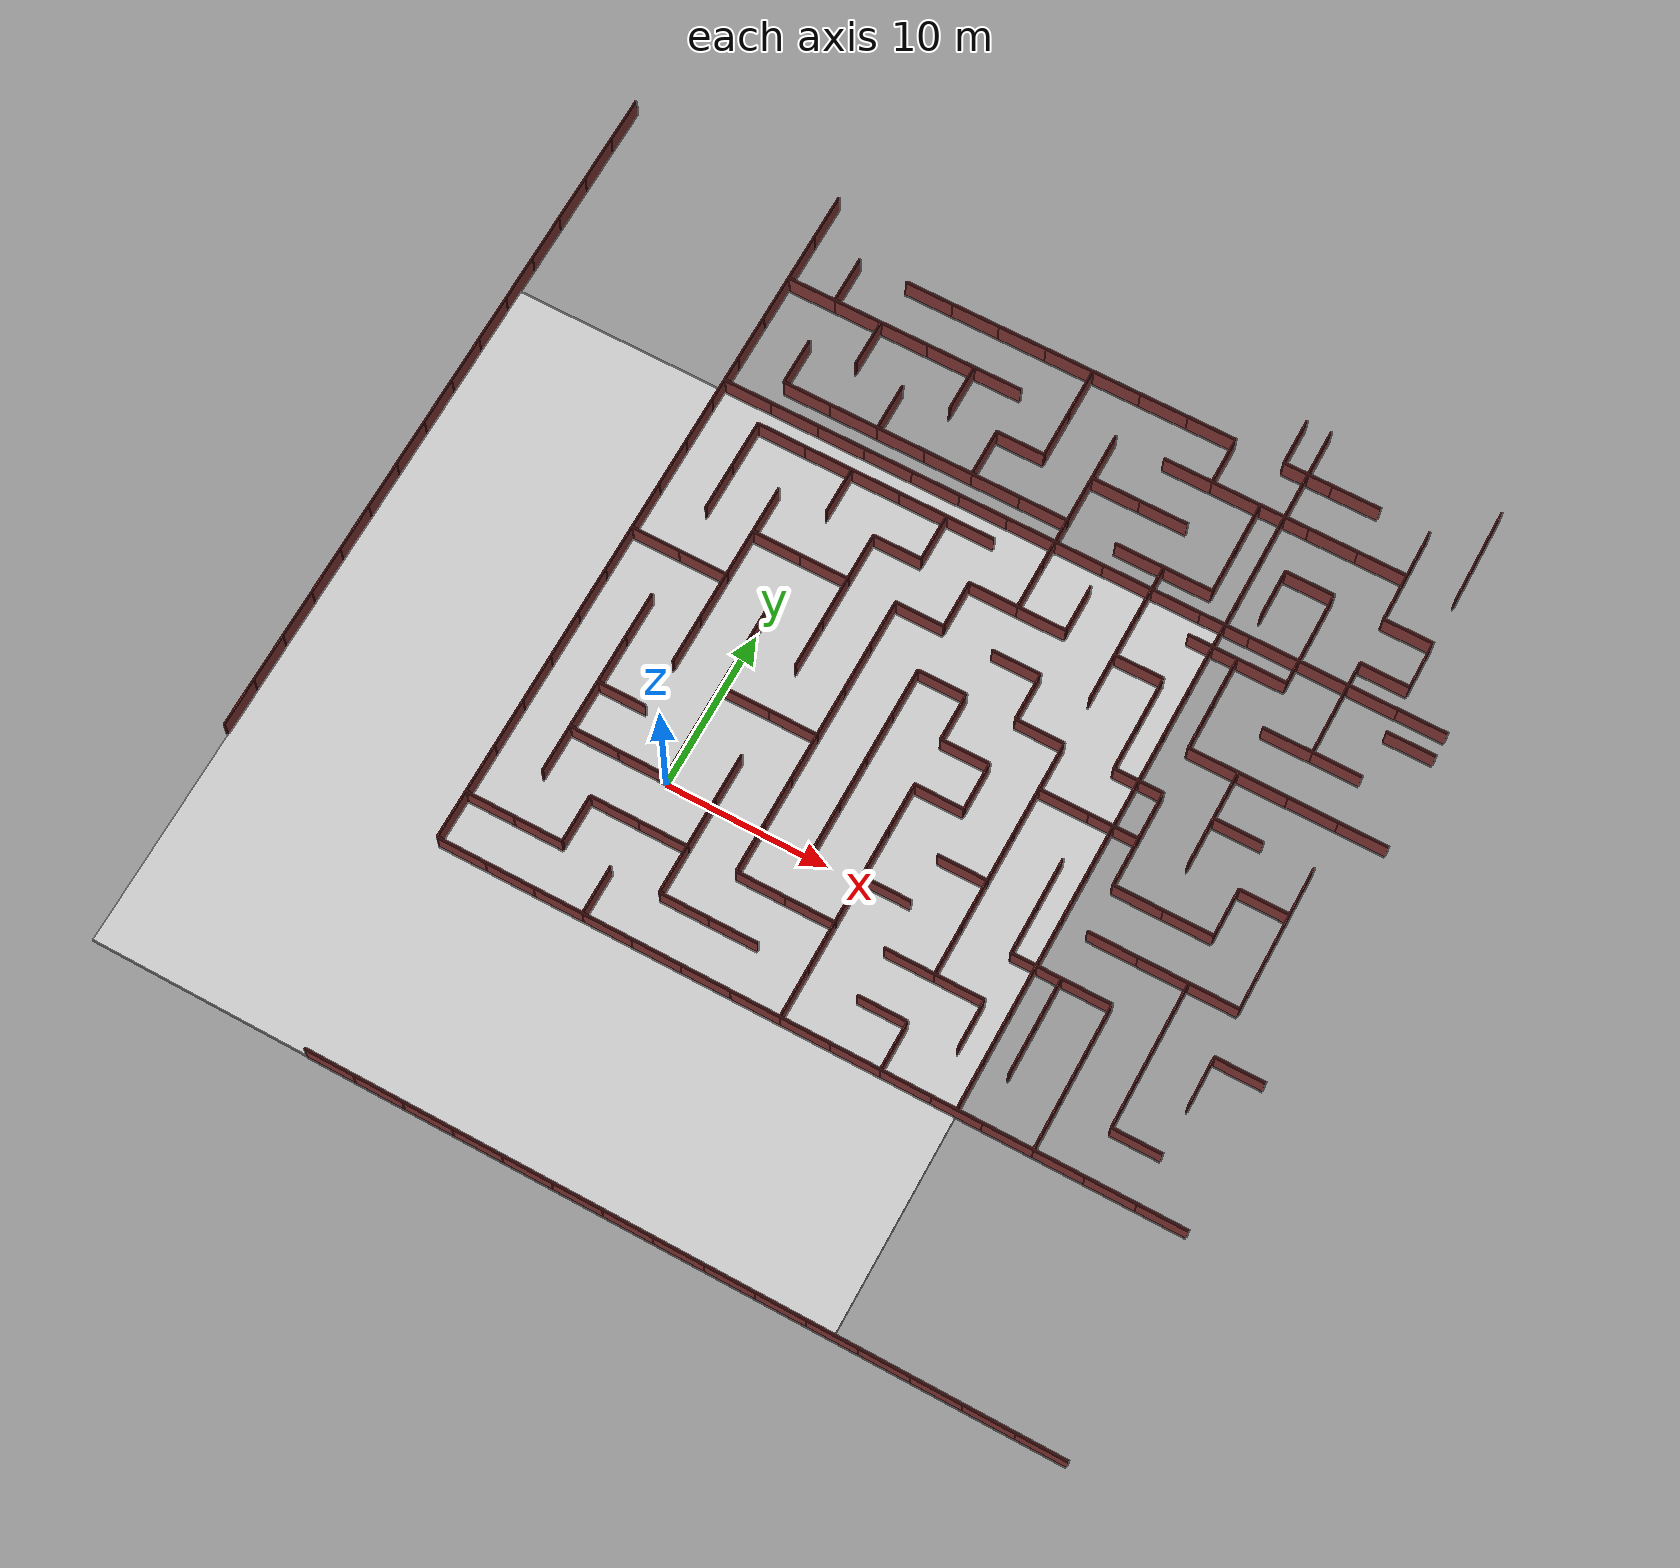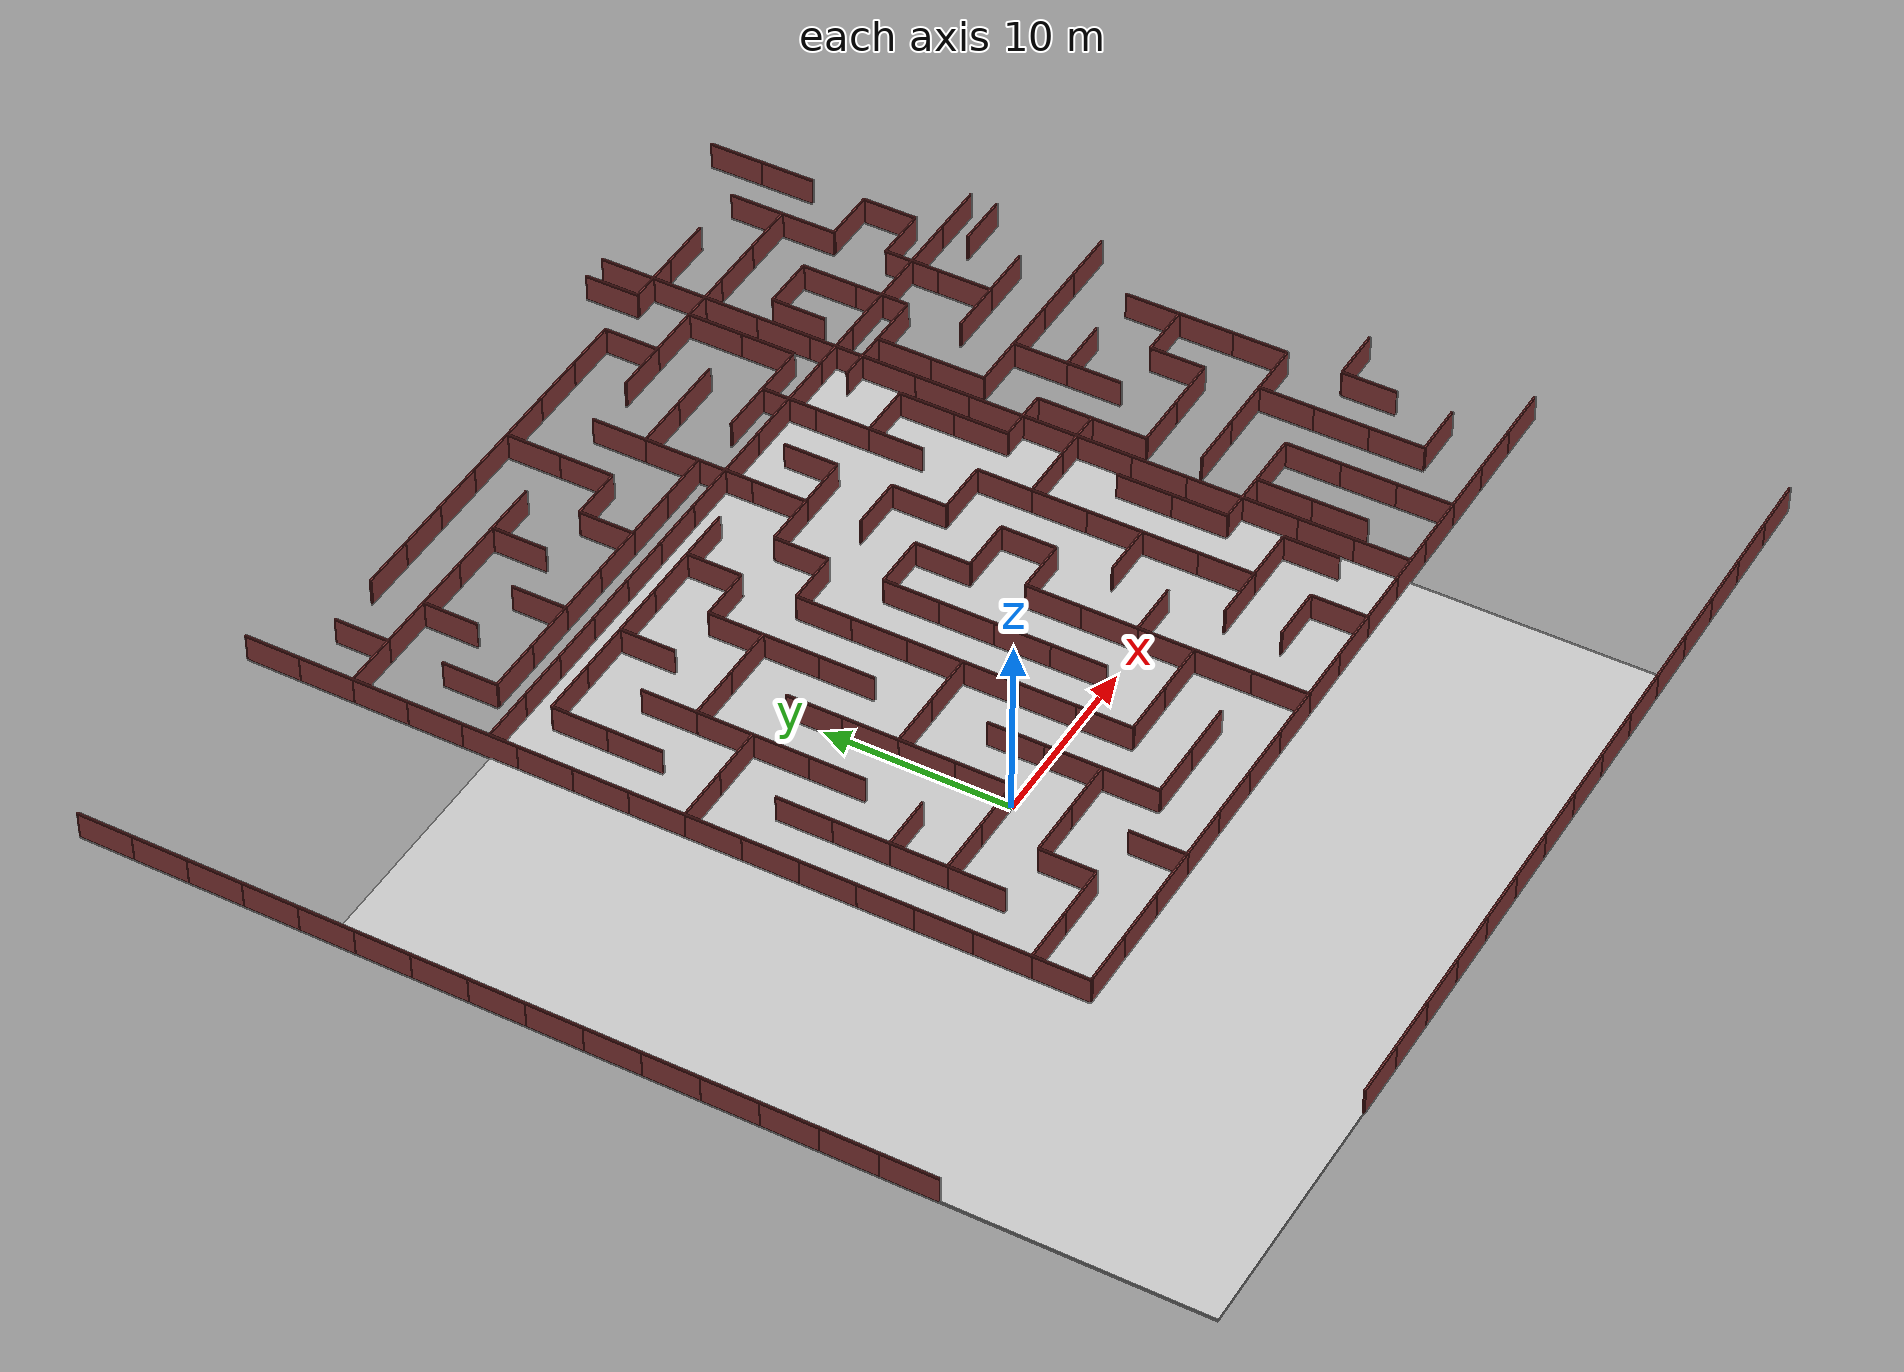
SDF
<?xml version="1.0" ?>
<sdf version="1.7">
  <world name="maze_world">

    <!-- Light -->
    <light name="sun" type="directional">
      <cast_shadows>true</cast_shadows>
      <pose>0 0 20 0 0 0</pose>
      <diffuse>1 1 1 1</diffuse>
      <direction>-0.5 0.5 -1</direction>
    </light>

    <!-- Large Ground -->
    <model name="ground">
      <static>true</static>
      <pose>0 0 0 0 0 0</pose>
      <link name="ground_link">
        <collision name="collision">
          <geometry><box><size>45 45 0.1</size></box></geometry>
        </collision>
        <visual name="visual">
          <geometry><box><size>45 45 0.1</size></box></geometry>
          <material><diffuse>0.8 0.8 0.8 1</diffuse></material>
        </visual>
      </link>
    </model>

    <model name="wall_n_1">
      <static>true</static>
      <pose>-7.5 -9.0 0.75 0 0 0</pose>
      <link name="link">
        <collision name="collision">
          <geometry><box><size>3 0.1 1.5</size></box></geometry>
        </collision>
        <visual name="visual">
          <geometry><box><size>3 0.1 1.5</size></box></geometry>
          <material><diffuse>0.5 0.2 0.2 1</diffuse></material>
        </visual>
      </link>
    </model>

    <model name="wall_w_2">
      <static>true</static>
      <pose>-9.0 -7.5 0.75 0 0 1.5708</pose>
      <link name="link">
        <collision name="collision">
          <geometry><box><size>3 0.1 1.5</size></box></geometry>
        </collision>
        <visual name="visual">
          <geometry><box><size>3 0.1 1.5</size></box></geometry>
          <material><diffuse>0.5 0.2 0.2 1</diffuse></material>
        </visual>
      </link>
    </model>

    <model name="wall_n_3">
      <static>true</static>
      <pose>-4.5 -9.0 0.75 0 0 0</pose>
      <link name="link">
        <collision name="collision">
          <geometry><box><size>3 0.1 1.5</size></box></geometry>
        </collision>
        <visual name="visual">
          <geometry><box><size>3 0.1 1.5</size></box></geometry>
          <material><diffuse>0.5 0.2 0.2 1</diffuse></material>
        </visual>
      </link>
    </model>

    <model name="wall_n_4">
      <static>true</static>
      <pose>-1.5 -9.0 0.75 0 0 0</pose>
      <link name="link">
        <collision name="collision">
          <geometry><box><size>3 0.1 1.5</size></box></geometry>
        </collision>
        <visual name="visual">
          <geometry><box><size>3 0.1 1.5</size></box></geometry>
          <material><diffuse>0.5 0.2 0.2 1</diffuse></material>
        </visual>
      </link>
    </model>

    <model name="wall_n_5">
      <static>true</static>
      <pose>1.5 -9.0 0.75 0 0 0</pose>
      <link name="link">
        <collision name="collision">
          <geometry><box><size>3 0.1 1.5</size></box></geometry>
        </collision>
        <visual name="visual">
          <geometry><box><size>3 0.1 1.5</size></box></geometry>
          <material><diffuse>0.5 0.2 0.2 1</diffuse></material>
        </visual>
      </link>
    </model>

    <model name="wall_w_6">
      <static>true</static>
      <pose>0.0 -7.5 0.75 0 0 1.5708</pose>
      <link name="link">
        <collision name="collision">
          <geometry><box><size>3 0.1 1.5</size></box></geometry>
        </collision>
        <visual name="visual">
          <geometry><box><size>3 0.1 1.5</size></box></geometry>
          <material><diffuse>0.5 0.2 0.2 1</diffuse></material>
        </visual>
      </link>
    </model>

    <model name="wall_n_7">
      <static>true</static>
      <pose>4.5 -9.0 0.75 0 0 0</pose>
      <link name="link">
        <collision name="collision">
          <geometry><box><size>3 0.1 1.5</size></box></geometry>
        </collision>
        <visual name="visual">
          <geometry><box><size>3 0.1 1.5</size></box></geometry>
          <material><diffuse>0.5 0.2 0.2 1</diffuse></material>
        </visual>
      </link>
    </model>

    <model name="wall_n_8">
      <static>true</static>
      <pose>7.5 -9.0 0.75 0 0 0</pose>
      <link name="link">
        <collision name="collision">
          <geometry><box><size>3 0.1 1.5</size></box></geometry>
        </collision>
        <visual name="visual">
          <geometry><box><size>3 0.1 1.5</size></box></geometry>
          <material><diffuse>0.5 0.2 0.2 1</diffuse></material>
        </visual>
      </link>
    </model>

    <model name="wall_n_9">
      <static>true</static>
      <pose>10.5 -9.0 0.75 0 0 0</pose>
      <link name="link">
        <collision name="collision">
          <geometry><box><size>3 0.1 1.5</size></box></geometry>
        </collision>
        <visual name="visual">
          <geometry><box><size>3 0.1 1.5</size></box></geometry>
          <material><diffuse>0.5 0.2 0.2 1</diffuse></material>
        </visual>
      </link>
    </model>

    <model name="wall_n_10">
      <static>true</static>
      <pose>13.5 -9.0 0.75 0 0 0</pose>
      <link name="link">
        <collision name="collision">
          <geometry><box><size>3 0.1 1.5</size></box></geometry>
        </collision>
        <visual name="visual">
          <geometry><box><size>3 0.1 1.5</size></box></geometry>
          <material><diffuse>0.5 0.2 0.2 1</diffuse></material>
        </visual>
      </link>
    </model>

    <model name="wall_w_11">
      <static>true</static>
      <pose>12.0 -7.5 0.75 0 0 1.5708</pose>
      <link name="link">
        <collision name="collision">
          <geometry><box><size>3 0.1 1.5</size></box></geometry>
        </collision>
        <visual name="visual">
          <geometry><box><size>3 0.1 1.5</size></box></geometry>
          <material><diffuse>0.5 0.2 0.2 1</diffuse></material>
        </visual>
      </link>
    </model>

    <model name="wall_n_12">
      <static>true</static>
      <pose>16.5 -9.0 0.75 0 0 0</pose>
      <link name="link">
        <collision name="collision">
          <geometry><box><size>3 0.1 1.5</size></box></geometry>
        </collision>
        <visual name="visual">
          <geometry><box><size>3 0.1 1.5</size></box></geometry>
          <material><diffuse>0.5 0.2 0.2 1</diffuse></material>
        </visual>
      </link>
    </model>

    <model name="wall_n_13">
      <static>true</static>
      <pose>19.5 -9.0 0.75 0 0 0</pose>
      <link name="link">
        <collision name="collision">
          <geometry><box><size>3 0.1 1.5</size></box></geometry>
        </collision>
        <visual name="visual">
          <geometry><box><size>3 0.1 1.5</size></box></geometry>
          <material><diffuse>0.5 0.2 0.2 1</diffuse></material>
        </visual>
      </link>
    </model>

    <model name="wall_w_14">
      <static>true</static>
      <pose>18.0 -7.5 0.75 0 0 1.5708</pose>
      <link name="link">
        <collision name="collision">
          <geometry><box><size>3 0.1 1.5</size></box></geometry>
        </collision>
        <visual name="visual">
          <geometry><box><size>3 0.1 1.5</size></box></geometry>
          <material><diffuse>0.5 0.2 0.2 1</diffuse></material>
        </visual>
      </link>
    </model>

    <model name="wall_n_15">
      <static>true</static>
      <pose>22.5 -9.0 0.75 0 0 0</pose>
      <link name="link">
        <collision name="collision">
          <geometry><box><size>3 0.1 1.5</size></box></geometry>
        </collision>
        <visual name="visual">
          <geometry><box><size>3 0.1 1.5</size></box></geometry>
          <material><diffuse>0.5 0.2 0.2 1</diffuse></material>
        </visual>
      </link>
    </model>

    <model name="wall_n_16">
      <static>true</static>
      <pose>25.5 -9.0 0.75 0 0 0</pose>
      <link name="link">
        <collision name="collision">
          <geometry><box><size>3 0.1 1.5</size></box></geometry>
        </collision>
        <visual name="visual">
          <geometry><box><size>3 0.1 1.5</size></box></geometry>
          <material><diffuse>0.5 0.2 0.2 1</diffuse></material>
        </visual>
      </link>
    </model>

    <model name="wall_n_17">
      <static>true</static>
      <pose>28.5 -9.0 0.75 0 0 0</pose>
      <link name="link">
        <collision name="collision">
          <geometry><box><size>3 0.1 1.5</size></box></geometry>
        </collision>
        <visual name="visual">
          <geometry><box><size>3 0.1 1.5</size></box></geometry>
          <material><diffuse>0.5 0.2 0.2 1</diffuse></material>
        </visual>
      </link>
    </model>

    <model name="wall_w_18">
      <static>true</static>
      <pose>27.0 -7.5 0.75 0 0 1.5708</pose>
      <link name="link">
        <collision name="collision">
          <geometry><box><size>3 0.1 1.5</size></box></geometry>
        </collision>
        <visual name="visual">
          <geometry><box><size>3 0.1 1.5</size></box></geometry>
          <material><diffuse>0.5 0.2 0.2 1</diffuse></material>
        </visual>
      </link>
    </model>

    <model name="wall_n_19">
      <static>true</static>
      <pose>31.5 -9.0 0.75 0 0 0</pose>
      <link name="link">
        <collision name="collision">
          <geometry><box><size>3 0.1 1.5</size></box></geometry>
        </collision>
        <visual name="visual">
          <geometry><box><size>3 0.1 1.5</size></box></geometry>
          <material><diffuse>0.5 0.2 0.2 1</diffuse></material>
        </visual>
      </link>
    </model>

    <model name="wall_n_20">
      <static>true</static>
      <pose>34.5 -9.0 0.75 0 0 0</pose>
      <link name="link">
        <collision name="collision">
          <geometry><box><size>3 0.1 1.5</size></box></geometry>
        </collision>
        <visual name="visual">
          <geometry><box><size>3 0.1 1.5</size></box></geometry>
          <material><diffuse>0.5 0.2 0.2 1</diffuse></material>
        </visual>
      </link>
    </model>

    <model name="wall_n_21">
      <static>true</static>
      <pose>-7.5 -6.0 0.75 0 0 0</pose>
      <link name="link">
        <collision name="collision">
          <geometry><box><size>3 0.1 1.5</size></box></geometry>
        </collision>
        <visual name="visual">
          <geometry><box><size>3 0.1 1.5</size></box></geometry>
          <material><diffuse>0.5 0.2 0.2 1</diffuse></material>
        </visual>
      </link>
    </model>

    <model name="wall_w_22">
      <static>true</static>
      <pose>-9.0 -4.5 0.75 0 0 1.5708</pose>
      <link name="link">
        <collision name="collision">
          <geometry><box><size>3 0.1 1.5</size></box></geometry>
        </collision>
        <visual name="visual">
          <geometry><box><size>3 0.1 1.5</size></box></geometry>
          <material><diffuse>0.5 0.2 0.2 1</diffuse></material>
        </visual>
      </link>
    </model>

    <model name="wall_n_23">
      <static>true</static>
      <pose>-4.5 -6.0 0.75 0 0 0</pose>
      <link name="link">
        <collision name="collision">
          <geometry><box><size>3 0.1 1.5</size></box></geometry>
        </collision>
        <visual name="visual">
          <geometry><box><size>3 0.1 1.5</size></box></geometry>
          <material><diffuse>0.5 0.2 0.2 1</diffuse></material>
        </visual>
      </link>
    </model>

    <model name="wall_w_24">
      <static>true</static>
      <pose>-3.0 -4.5 0.75 0 0 1.5708</pose>
      <link name="link">
        <collision name="collision">
          <geometry><box><size>3 0.1 1.5</size></box></geometry>
        </collision>
        <visual name="visual">
          <geometry><box><size>3 0.1 1.5</size></box></geometry>
          <material><diffuse>0.5 0.2 0.2 1</diffuse></material>
        </visual>
      </link>
    </model>

    <model name="wall_n_25">
      <static>true</static>
      <pose>4.5 -6.0 0.75 0 0 0</pose>
      <link name="link">
        <collision name="collision">
          <geometry><box><size>3 0.1 1.5</size></box></geometry>
        </collision>
        <visual name="visual">
          <geometry><box><size>3 0.1 1.5</size></box></geometry>
          <material><diffuse>0.5 0.2 0.2 1</diffuse></material>
        </visual>
      </link>
    </model>

    <model name="wall_w_26">
      <static>true</static>
      <pose>3.0 -4.5 0.75 0 0 1.5708</pose>
      <link name="link">
        <collision name="collision">
          <geometry><box><size>3 0.1 1.5</size></box></geometry>
        </collision>
        <visual name="visual">
          <geometry><box><size>3 0.1 1.5</size></box></geometry>
          <material><diffuse>0.5 0.2 0.2 1</diffuse></material>
        </visual>
      </link>
    </model>

    <model name="wall_n_27">
      <static>true</static>
      <pose>7.5 -6.0 0.75 0 0 0</pose>
      <link name="link">
        <collision name="collision">
          <geometry><box><size>3 0.1 1.5</size></box></geometry>
        </collision>
        <visual name="visual">
          <geometry><box><size>3 0.1 1.5</size></box></geometry>
          <material><diffuse>0.5 0.2 0.2 1</diffuse></material>
        </visual>
      </link>
    </model>

    <model name="wall_w_28">
      <static>true</static>
      <pose>12.0 -4.5 0.75 0 0 1.5708</pose>
      <link name="link">
        <collision name="collision">
          <geometry><box><size>3 0.1 1.5</size></box></geometry>
        </collision>
        <visual name="visual">
          <geometry><box><size>3 0.1 1.5</size></box></geometry>
          <material><diffuse>0.5 0.2 0.2 1</diffuse></material>
        </visual>
      </link>
    </model>

    <model name="wall_n_29">
      <static>true</static>
      <pose>16.5 -6.0 0.75 0 0 0</pose>
      <link name="link">
        <collision name="collision">
          <geometry><box><size>3 0.1 1.5</size></box></geometry>
        </collision>
        <visual name="visual">
          <geometry><box><size>3 0.1 1.5</size></box></geometry>
          <material><diffuse>0.5 0.2 0.2 1</diffuse></material>
        </visual>
      </link>
    </model>

    <model name="wall_w_30">
      <static>true</static>
      <pose>21.0 -4.5 0.75 0 0 1.5708</pose>
      <link name="link">
        <collision name="collision">
          <geometry><box><size>3 0.1 1.5</size></box></geometry>
        </collision>
        <visual name="visual">
          <geometry><box><size>3 0.1 1.5</size></box></geometry>
          <material><diffuse>0.5 0.2 0.2 1</diffuse></material>
        </visual>
      </link>
    </model>

    <model name="wall_w_31">
      <static>true</static>
      <pose>24.0 -4.5 0.75 0 0 1.5708</pose>
      <link name="link">
        <collision name="collision">
          <geometry><box><size>3 0.1 1.5</size></box></geometry>
        </collision>
        <visual name="visual">
          <geometry><box><size>3 0.1 1.5</size></box></geometry>
          <material><diffuse>0.5 0.2 0.2 1</diffuse></material>
        </visual>
      </link>
    </model>

    <model name="wall_w_32">
      <static>true</static>
      <pose>27.0 -4.5 0.75 0 0 1.5708</pose>
      <link name="link">
        <collision name="collision">
          <geometry><box><size>3 0.1 1.5</size></box></geometry>
        </collision>
        <visual name="visual">
          <geometry><box><size>3 0.1 1.5</size></box></geometry>
          <material><diffuse>0.5 0.2 0.2 1</diffuse></material>
        </visual>
      </link>
    </model>

    <model name="wall_n_33">
      <static>true</static>
      <pose>31.5 -6.0 0.75 0 0 0</pose>
      <link name="link">
        <collision name="collision">
          <geometry><box><size>3 0.1 1.5</size></box></geometry>
        </collision>
        <visual name="visual">
          <geometry><box><size>3 0.1 1.5</size></box></geometry>
          <material><diffuse>0.5 0.2 0.2 1</diffuse></material>
        </visual>
      </link>
    </model>

    <model name="wall_w_34">
      <static>true</static>
      <pose>30.0 -4.5 0.75 0 0 1.5708</pose>
      <link name="link">
        <collision name="collision">
          <geometry><box><size>3 0.1 1.5</size></box></geometry>
        </collision>
        <visual name="visual">
          <geometry><box><size>3 0.1 1.5</size></box></geometry>
          <material><diffuse>0.5 0.2 0.2 1</diffuse></material>
        </visual>
      </link>
    </model>

    <model name="wall_w_35">
      <static>true</static>
      <pose>-9.0 -1.5 0.75 0 0 1.5708</pose>
      <link name="link">
        <collision name="collision">
          <geometry><box><size>3 0.1 1.5</size></box></geometry>
        </collision>
        <visual name="visual">
          <geometry><box><size>3 0.1 1.5</size></box></geometry>
          <material><diffuse>0.5 0.2 0.2 1</diffuse></material>
        </visual>
      </link>
    </model>

    <model name="wall_w_36">
      <static>true</static>
      <pose>-6.0 -1.5 0.75 0 0 1.5708</pose>
      <link name="link">
        <collision name="collision">
          <geometry><box><size>3 0.1 1.5</size></box></geometry>
        </collision>
        <visual name="visual">
          <geometry><box><size>3 0.1 1.5</size></box></geometry>
          <material><diffuse>0.5 0.2 0.2 1</diffuse></material>
        </visual>
      </link>
    </model>

    <model name="wall_n_37">
      <static>true</static>
      <pose>-1.5 -3.0 0.75 0 0 0</pose>
      <link name="link">
        <collision name="collision">
          <geometry><box><size>3 0.1 1.5</size></box></geometry>
        </collision>
        <visual name="visual">
          <geometry><box><size>3 0.1 1.5</size></box></geometry>
          <material><diffuse>0.5 0.2 0.2 1</diffuse></material>
        </visual>
      </link>
    </model>

    <model name="wall_n_38">
      <static>true</static>
      <pose>1.5 -3.0 0.75 0 0 0</pose>
      <link name="link">
        <collision name="collision">
          <geometry><box><size>3 0.1 1.5</size></box></geometry>
        </collision>
        <visual name="visual">
          <geometry><box><size>3 0.1 1.5</size></box></geometry>
          <material><diffuse>0.5 0.2 0.2 1</diffuse></material>
        </visual>
      </link>
    </model>

    <model name="wall_w_39">
      <static>true</static>
      <pose>3.0 -1.5 0.75 0 0 1.5708</pose>
      <link name="link">
        <collision name="collision">
          <geometry><box><size>3 0.1 1.5</size></box></geometry>
        </collision>
        <visual name="visual">
          <geometry><box><size>3 0.1 1.5</size></box></geometry>
          <material><diffuse>0.5 0.2 0.2 1</diffuse></material>
        </visual>
      </link>
    </model>

    <model name="wall_n_40">
      <static>true</static>
      <pose>7.5 -3.0 0.75 0 0 0</pose>
      <link name="link">
        <collision name="collision">
          <geometry><box><size>3 0.1 1.5</size></box></geometry>
        </collision>
        <visual name="visual">
          <geometry><box><size>3 0.1 1.5</size></box></geometry>
          <material><diffuse>0.5 0.2 0.2 1</diffuse></material>
        </visual>
      </link>
    </model>

    <model name="wall_w_41">
      <static>true</static>
      <pose>6.0 -1.5 0.75 0 0 1.5708</pose>
      <link name="link">
        <collision name="collision">
          <geometry><box><size>3 0.1 1.5</size></box></geometry>
        </collision>
        <visual name="visual">
          <geometry><box><size>3 0.1 1.5</size></box></geometry>
          <material><diffuse>0.5 0.2 0.2 1</diffuse></material>
        </visual>
      </link>
    </model>

    <model name="wall_n_42">
      <static>true</static>
      <pose>10.5 -3.0 0.75 0 0 0</pose>
      <link name="link">
        <collision name="collision">
          <geometry><box><size>3 0.1 1.5</size></box></geometry>
        </collision>
        <visual name="visual">
          <geometry><box><size>3 0.1 1.5</size></box></geometry>
          <material><diffuse>0.5 0.2 0.2 1</diffuse></material>
        </visual>
      </link>
    </model>

    <model name="wall_w_43">
      <static>true</static>
      <pose>12.0 -1.5 0.75 0 0 1.5708</pose>
      <link name="link">
        <collision name="collision">
          <geometry><box><size>3 0.1 1.5</size></box></geometry>
        </collision>
        <visual name="visual">
          <geometry><box><size>3 0.1 1.5</size></box></geometry>
          <material><diffuse>0.5 0.2 0.2 1</diffuse></material>
        </visual>
      </link>
    </model>

    <model name="wall_n_44">
      <static>true</static>
      <pose>16.5 -3.0 0.75 0 0 0</pose>
      <link name="link">
        <collision name="collision">
          <geometry><box><size>3 0.1 1.5</size></box></geometry>
        </collision>
        <visual name="visual">
          <geometry><box><size>3 0.1 1.5</size></box></geometry>
          <material><diffuse>0.5 0.2 0.2 1</diffuse></material>
        </visual>
      </link>
    </model>

    <model name="wall_n_45">
      <static>true</static>
      <pose>19.5 -3.0 0.75 0 0 0</pose>
      <link name="link">
        <collision name="collision">
          <geometry><box><size>3 0.1 1.5</size></box></geometry>
        </collision>
        <visual name="visual">
          <geometry><box><size>3 0.1 1.5</size></box></geometry>
          <material><diffuse>0.5 0.2 0.2 1</diffuse></material>
        </visual>
      </link>
    </model>

    <model name="wall_w_46">
      <static>true</static>
      <pose>18.0 -1.5 0.75 0 0 1.5708</pose>
      <link name="link">
        <collision name="collision">
          <geometry><box><size>3 0.1 1.5</size></box></geometry>
        </collision>
        <visual name="visual">
          <geometry><box><size>3 0.1 1.5</size></box></geometry>
          <material><diffuse>0.5 0.2 0.2 1</diffuse></material>
        </visual>
      </link>
    </model>

    <model name="wall_w_47">
      <static>true</static>
      <pose>24.0 -1.5 0.75 0 0 1.5708</pose>
      <link name="link">
        <collision name="collision">
          <geometry><box><size>3 0.1 1.5</size></box></geometry>
        </collision>
        <visual name="visual">
          <geometry><box><size>3 0.1 1.5</size></box></geometry>
          <material><diffuse>0.5 0.2 0.2 1</diffuse></material>
        </visual>
      </link>
    </model>

    <model name="wall_w_48">
      <static>true</static>
      <pose>27.0 -1.5 0.75 0 0 1.5708</pose>
      <link name="link">
        <collision name="collision">
          <geometry><box><size>3 0.1 1.5</size></box></geometry>
        </collision>
        <visual name="visual">
          <geometry><box><size>3 0.1 1.5</size></box></geometry>
          <material><diffuse>0.5 0.2 0.2 1</diffuse></material>
        </visual>
      </link>
    </model>

    <model name="wall_w_49">
      <static>true</static>
      <pose>30.0 -1.5 0.75 0 0 1.5708</pose>
      <link name="link">
        <collision name="collision">
          <geometry><box><size>3 0.1 1.5</size></box></geometry>
        </collision>
        <visual name="visual">
          <geometry><box><size>3 0.1 1.5</size></box></geometry>
          <material><diffuse>0.5 0.2 0.2 1</diffuse></material>
        </visual>
      </link>
    </model>

    <model name="wall_w_50">
      <static>true</static>
      <pose>33.0 -1.5 0.75 0 0 1.5708</pose>
      <link name="link">
        <collision name="collision">
          <geometry><box><size>3 0.1 1.5</size></box></geometry>
        </collision>
        <visual name="visual">
          <geometry><box><size>3 0.1 1.5</size></box></geometry>
          <material><diffuse>0.5 0.2 0.2 1</diffuse></material>
        </visual>
      </link>
    </model>

    <model name="wall_w_51">
      <static>true</static>
      <pose>-9.0 1.5 0.75 0 0 1.5708</pose>
      <link name="link">
        <collision name="collision">
          <geometry><box><size>3 0.1 1.5</size></box></geometry>
        </collision>
        <visual name="visual">
          <geometry><box><size>3 0.1 1.5</size></box></geometry>
          <material><diffuse>0.5 0.2 0.2 1</diffuse></material>
        </visual>
      </link>
    </model>

    <model name="wall_n_52">
      <static>true</static>
      <pose>-4.5 0.0 0.75 0 0 0</pose>
      <link name="link">
        <collision name="collision">
          <geometry><box><size>3 0.1 1.5</size></box></geometry>
        </collision>
        <visual name="visual">
          <geometry><box><size>3 0.1 1.5</size></box></geometry>
          <material><diffuse>0.5 0.2 0.2 1</diffuse></material>
        </visual>
      </link>
    </model>

    <model name="wall_w_53">
      <static>true</static>
      <pose>-6.0 1.5 0.75 0 0 1.5708</pose>
      <link name="link">
        <collision name="collision">
          <geometry><box><size>3 0.1 1.5</size></box></geometry>
        </collision>
        <visual name="visual">
          <geometry><box><size>3 0.1 1.5</size></box></geometry>
          <material><diffuse>0.5 0.2 0.2 1</diffuse></material>
        </visual>
      </link>
    </model>

    <model name="wall_n_54">
      <static>true</static>
      <pose>-1.5 0.0 0.75 0 0 0</pose>
      <link name="link">
        <collision name="collision">
          <geometry><box><size>3 0.1 1.5</size></box></geometry>
        </collision>
        <visual name="visual">
          <geometry><box><size>3 0.1 1.5</size></box></geometry>
          <material><diffuse>0.5 0.2 0.2 1</diffuse></material>
        </visual>
      </link>
    </model>

    <model name="wall_w_55">
      <static>true</static>
      <pose>0.0 1.5 0.75 0 0 1.5708</pose>
      <link name="link">
        <collision name="collision">
          <geometry><box><size>3 0.1 1.5</size></box></geometry>
        </collision>
        <visual name="visual">
          <geometry><box><size>3 0.1 1.5</size></box></geometry>
          <material><diffuse>0.5 0.2 0.2 1</diffuse></material>
        </visual>
      </link>
    </model>

    <model name="wall_w_56">
      <static>true</static>
      <pose>3.0 1.5 0.75 0 0 1.5708</pose>
      <link name="link">
        <collision name="collision">
          <geometry><box><size>3 0.1 1.5</size></box></geometry>
        </collision>
        <visual name="visual">
          <geometry><box><size>3 0.1 1.5</size></box></geometry>
          <material><diffuse>0.5 0.2 0.2 1</diffuse></material>
        </visual>
      </link>
    </model>

    <model name="wall_w_57">
      <static>true</static>
      <pose>6.0 1.5 0.75 0 0 1.5708</pose>
      <link name="link">
        <collision name="collision">
          <geometry><box><size>3 0.1 1.5</size></box></geometry>
        </collision>
        <visual name="visual">
          <geometry><box><size>3 0.1 1.5</size></box></geometry>
          <material><diffuse>0.5 0.2 0.2 1</diffuse></material>
        </visual>
      </link>
    </model>

    <model name="wall_w_58">
      <static>true</static>
      <pose>9.0 1.5 0.75 0 0 1.5708</pose>
      <link name="link">
        <collision name="collision">
          <geometry><box><size>3 0.1 1.5</size></box></geometry>
        </collision>
        <visual name="visual">
          <geometry><box><size>3 0.1 1.5</size></box></geometry>
          <material><diffuse>0.5 0.2 0.2 1</diffuse></material>
        </visual>
      </link>
    </model>

    <model name="wall_n_59">
      <static>true</static>
      <pose>13.5 0.0 0.75 0 0 0</pose>
      <link name="link">
        <collision name="collision">
          <geometry><box><size>3 0.1 1.5</size></box></geometry>
        </collision>
        <visual name="visual">
          <geometry><box><size>3 0.1 1.5</size></box></geometry>
          <material><diffuse>0.5 0.2 0.2 1</diffuse></material>
        </visual>
      </link>
    </model>

    <model name="wall_w_60">
      <static>true</static>
      <pose>12.0 1.5 0.75 0 0 1.5708</pose>
      <link name="link">
        <collision name="collision">
          <geometry><box><size>3 0.1 1.5</size></box></geometry>
        </collision>
        <visual name="visual">
          <geometry><box><size>3 0.1 1.5</size></box></geometry>
          <material><diffuse>0.5 0.2 0.2 1</diffuse></material>
        </visual>
      </link>
    </model>

    <model name="wall_w_61">
      <static>true</static>
      <pose>18.0 1.5 0.75 0 0 1.5708</pose>
      <link name="link">
        <collision name="collision">
          <geometry><box><size>3 0.1 1.5</size></box></geometry>
        </collision>
        <visual name="visual">
          <geometry><box><size>3 0.1 1.5</size></box></geometry>
          <material><diffuse>0.5 0.2 0.2 1</diffuse></material>
        </visual>
      </link>
    </model>

    <model name="wall_n_62">
      <static>true</static>
      <pose>22.5 0.0 0.75 0 0 0</pose>
      <link name="link">
        <collision name="collision">
          <geometry><box><size>3 0.1 1.5</size></box></geometry>
        </collision>
        <visual name="visual">
          <geometry><box><size>3 0.1 1.5</size></box></geometry>
          <material><diffuse>0.5 0.2 0.2 1</diffuse></material>
        </visual>
      </link>
    </model>

    <model name="wall_w_63">
      <static>true</static>
      <pose>21.0 1.5 0.75 0 0 1.5708</pose>
      <link name="link">
        <collision name="collision">
          <geometry><box><size>3 0.1 1.5</size></box></geometry>
        </collision>
        <visual name="visual">
          <geometry><box><size>3 0.1 1.5</size></box></geometry>
          <material><diffuse>0.5 0.2 0.2 1</diffuse></material>
        </visual>
      </link>
    </model>

    <model name="wall_n_64">
      <static>true</static>
      <pose>25.5 0.0 0.75 0 0 0</pose>
      <link name="link">
        <collision name="collision">
          <geometry><box><size>3 0.1 1.5</size></box></geometry>
        </collision>
        <visual name="visual">
          <geometry><box><size>3 0.1 1.5</size></box></geometry>
          <material><diffuse>0.5 0.2 0.2 1</diffuse></material>
        </visual>
      </link>
    </model>

    <model name="wall_w_65">
      <static>true</static>
      <pose>30.0 1.5 0.75 0 0 1.5708</pose>
      <link name="link">
        <collision name="collision">
          <geometry><box><size>3 0.1 1.5</size></box></geometry>
        </collision>
        <visual name="visual">
          <geometry><box><size>3 0.1 1.5</size></box></geometry>
          <material><diffuse>0.5 0.2 0.2 1</diffuse></material>
        </visual>
      </link>
    </model>

    <model name="wall_n_66">
      <static>true</static>
      <pose>34.5 0.0 0.75 0 0 0</pose>
      <link name="link">
        <collision name="collision">
          <geometry><box><size>3 0.1 1.5</size></box></geometry>
        </collision>
        <visual name="visual">
          <geometry><box><size>3 0.1 1.5</size></box></geometry>
          <material><diffuse>0.5 0.2 0.2 1</diffuse></material>
        </visual>
      </link>
    </model>

    <model name="wall_w_67">
      <static>true</static>
      <pose>-9.0 4.5 0.75 0 0 1.5708</pose>
      <link name="link">
        <collision name="collision">
          <geometry><box><size>3 0.1 1.5</size></box></geometry>
        </collision>
        <visual name="visual">
          <geometry><box><size>3 0.1 1.5</size></box></geometry>
          <material><diffuse>0.5 0.2 0.2 1</diffuse></material>
        </visual>
      </link>
    </model>

    <model name="wall_n_68">
      <static>true</static>
      <pose>-4.5 3.0 0.75 0 0 0</pose>
      <link name="link">
        <collision name="collision">
          <geometry><box><size>3 0.1 1.5</size></box></geometry>
        </collision>
        <visual name="visual">
          <geometry><box><size>3 0.1 1.5</size></box></geometry>
          <material><diffuse>0.5 0.2 0.2 1</diffuse></material>
        </visual>
      </link>
    </model>

    <model name="wall_w_69">
      <static>true</static>
      <pose>-6.0 4.5 0.75 0 0 1.5708</pose>
      <link name="link">
        <collision name="collision">
          <geometry><box><size>3 0.1 1.5</size></box></geometry>
        </collision>
        <visual name="visual">
          <geometry><box><size>3 0.1 1.5</size></box></geometry>
          <material><diffuse>0.5 0.2 0.2 1</diffuse></material>
        </visual>
      </link>
    </model>

    <model name="wall_w_70">
      <static>true</static>
      <pose>0.0 4.5 0.75 0 0 1.5708</pose>
      <link name="link">
        <collision name="collision">
          <geometry><box><size>3 0.1 1.5</size></box></geometry>
        </collision>
        <visual name="visual">
          <geometry><box><size>3 0.1 1.5</size></box></geometry>
          <material><diffuse>0.5 0.2 0.2 1</diffuse></material>
        </visual>
      </link>
    </model>

    <model name="wall_w_71">
      <static>true</static>
      <pose>6.0 4.5 0.75 0 0 1.5708</pose>
      <link name="link">
        <collision name="collision">
          <geometry><box><size>3 0.1 1.5</size></box></geometry>
        </collision>
        <visual name="visual">
          <geometry><box><size>3 0.1 1.5</size></box></geometry>
          <material><diffuse>0.5 0.2 0.2 1</diffuse></material>
        </visual>
      </link>
    </model>

    <model name="wall_w_72">
      <static>true</static>
      <pose>9.0 4.5 0.75 0 0 1.5708</pose>
      <link name="link">
        <collision name="collision">
          <geometry><box><size>3 0.1 1.5</size></box></geometry>
        </collision>
        <visual name="visual">
          <geometry><box><size>3 0.1 1.5</size></box></geometry>
          <material><diffuse>0.5 0.2 0.2 1</diffuse></material>
        </visual>
      </link>
    </model>

    <model name="wall_w_73">
      <static>true</static>
      <pose>12.0 4.5 0.75 0 0 1.5708</pose>
      <link name="link">
        <collision name="collision">
          <geometry><box><size>3 0.1 1.5</size></box></geometry>
        </collision>
        <visual name="visual">
          <geometry><box><size>3 0.1 1.5</size></box></geometry>
          <material><diffuse>0.5 0.2 0.2 1</diffuse></material>
        </visual>
      </link>
    </model>

    <model name="wall_n_74">
      <static>true</static>
      <pose>16.5 3.0 0.75 0 0 0</pose>
      <link name="link">
        <collision name="collision">
          <geometry><box><size>3 0.1 1.5</size></box></geometry>
        </collision>
        <visual name="visual">
          <geometry><box><size>3 0.1 1.5</size></box></geometry>
          <material><diffuse>0.5 0.2 0.2 1</diffuse></material>
        </visual>
      </link>
    </model>

    <model name="wall_w_75">
      <static>true</static>
      <pose>18.0 4.5 0.75 0 0 1.5708</pose>
      <link name="link">
        <collision name="collision">
          <geometry><box><size>3 0.1 1.5</size></box></geometry>
        </collision>
        <visual name="visual">
          <geometry><box><size>3 0.1 1.5</size></box></geometry>
          <material><diffuse>0.5 0.2 0.2 1</diffuse></material>
        </visual>
      </link>
    </model>

    <model name="wall_w_76">
      <static>true</static>
      <pose>21.0 4.5 0.75 0 0 1.5708</pose>
      <link name="link">
        <collision name="collision">
          <geometry><box><size>3 0.1 1.5</size></box></geometry>
        </collision>
        <visual name="visual">
          <geometry><box><size>3 0.1 1.5</size></box></geometry>
          <material><diffuse>0.5 0.2 0.2 1</diffuse></material>
        </visual>
      </link>
    </model>

    <model name="wall_n_77">
      <static>true</static>
      <pose>25.5 3.0 0.75 0 0 0</pose>
      <link name="link">
        <collision name="collision">
          <geometry><box><size>3 0.1 1.5</size></box></geometry>
        </collision>
        <visual name="visual">
          <geometry><box><size>3 0.1 1.5</size></box></geometry>
          <material><diffuse>0.5 0.2 0.2 1</diffuse></material>
        </visual>
      </link>
    </model>

    <model name="wall_n_78">
      <static>true</static>
      <pose>28.5 3.0 0.75 0 0 0</pose>
      <link name="link">
        <collision name="collision">
          <geometry><box><size>3 0.1 1.5</size></box></geometry>
        </collision>
        <visual name="visual">
          <geometry><box><size>3 0.1 1.5</size></box></geometry>
          <material><diffuse>0.5 0.2 0.2 1</diffuse></material>
        </visual>
      </link>
    </model>

    <model name="wall_n_79">
      <static>true</static>
      <pose>31.5 3.0 0.75 0 0 0</pose>
      <link name="link">
        <collision name="collision">
          <geometry><box><size>3 0.1 1.5</size></box></geometry>
        </collision>
        <visual name="visual">
          <geometry><box><size>3 0.1 1.5</size></box></geometry>
          <material><diffuse>0.5 0.2 0.2 1</diffuse></material>
        </visual>
      </link>
    </model>

    <model name="wall_w_80">
      <static>true</static>
      <pose>33.0 4.5 0.75 0 0 1.5708</pose>
      <link name="link">
        <collision name="collision">
          <geometry><box><size>3 0.1 1.5</size></box></geometry>
        </collision>
        <visual name="visual">
          <geometry><box><size>3 0.1 1.5</size></box></geometry>
          <material><diffuse>0.5 0.2 0.2 1</diffuse></material>
        </visual>
      </link>
    </model>

    <model name="wall_w_81">
      <static>true</static>
      <pose>-9.0 7.5 0.75 0 0 1.5708</pose>
      <link name="link">
        <collision name="collision">
          <geometry><box><size>3 0.1 1.5</size></box></geometry>
        </collision>
        <visual name="visual">
          <geometry><box><size>3 0.1 1.5</size></box></geometry>
          <material><diffuse>0.5 0.2 0.2 1</diffuse></material>
        </visual>
      </link>
    </model>

    <model name="wall_w_82">
      <static>true</static>
      <pose>-6.0 7.5 0.75 0 0 1.5708</pose>
      <link name="link">
        <collision name="collision">
          <geometry><box><size>3 0.1 1.5</size></box></geometry>
        </collision>
        <visual name="visual">
          <geometry><box><size>3 0.1 1.5</size></box></geometry>
          <material><diffuse>0.5 0.2 0.2 1</diffuse></material>
        </visual>
      </link>
    </model>

    <model name="wall_w_83">
      <static>true</static>
      <pose>-3.0 7.5 0.75 0 0 1.5708</pose>
      <link name="link">
        <collision name="collision">
          <geometry><box><size>3 0.1 1.5</size></box></geometry>
        </collision>
        <visual name="visual">
          <geometry><box><size>3 0.1 1.5</size></box></geometry>
          <material><diffuse>0.5 0.2 0.2 1</diffuse></material>
        </visual>
      </link>
    </model>

    <model name="wall_n_84">
      <static>true</static>
      <pose>1.5 6.0 0.75 0 0 0</pose>
      <link name="link">
        <collision name="collision">
          <geometry><box><size>3 0.1 1.5</size></box></geometry>
        </collision>
        <visual name="visual">
          <geometry><box><size>3 0.1 1.5</size></box></geometry>
          <material><diffuse>0.5 0.2 0.2 1</diffuse></material>
        </visual>
      </link>
    </model>

    <model name="wall_w_85">
      <static>true</static>
      <pose>0.0 7.5 0.75 0 0 1.5708</pose>
      <link name="link">
        <collision name="collision">
          <geometry><box><size>3 0.1 1.5</size></box></geometry>
        </collision>
        <visual name="visual">
          <geometry><box><size>3 0.1 1.5</size></box></geometry>
          <material><diffuse>0.5 0.2 0.2 1</diffuse></material>
        </visual>
      </link>
    </model>

    <model name="wall_n_86">
      <static>true</static>
      <pose>4.5 6.0 0.75 0 0 0</pose>
      <link name="link">
        <collision name="collision">
          <geometry><box><size>3 0.1 1.5</size></box></geometry>
        </collision>
        <visual name="visual">
          <geometry><box><size>3 0.1 1.5</size></box></geometry>
          <material><diffuse>0.5 0.2 0.2 1</diffuse></material>
        </visual>
      </link>
    </model>

    <model name="wall_w_87">
      <static>true</static>
      <pose>6.0 7.5 0.75 0 0 1.5708</pose>
      <link name="link">
        <collision name="collision">
          <geometry><box><size>3 0.1 1.5</size></box></geometry>
        </collision>
        <visual name="visual">
          <geometry><box><size>3 0.1 1.5</size></box></geometry>
          <material><diffuse>0.5 0.2 0.2 1</diffuse></material>
        </visual>
      </link>
    </model>

    <model name="wall_w_88">
      <static>true</static>
      <pose>9.0 7.5 0.75 0 0 1.5708</pose>
      <link name="link">
        <collision name="collision">
          <geometry><box><size>3 0.1 1.5</size></box></geometry>
        </collision>
        <visual name="visual">
          <geometry><box><size>3 0.1 1.5</size></box></geometry>
          <material><diffuse>0.5 0.2 0.2 1</diffuse></material>
        </visual>
      </link>
    </model>

    <model name="wall_n_89">
      <static>true</static>
      <pose>13.5 6.0 0.75 0 0 0</pose>
      <link name="link">
        <collision name="collision">
          <geometry><box><size>3 0.1 1.5</size></box></geometry>
        </collision>
        <visual name="visual">
          <geometry><box><size>3 0.1 1.5</size></box></geometry>
          <material><diffuse>0.5 0.2 0.2 1</diffuse></material>
        </visual>
      </link>
    </model>

    <model name="wall_w_90">
      <static>true</static>
      <pose>15.0 7.5 0.75 0 0 1.5708</pose>
      <link name="link">
        <collision name="collision">
          <geometry><box><size>3 0.1 1.5</size></box></geometry>
        </collision>
        <visual name="visual">
          <geometry><box><size>3 0.1 1.5</size></box></geometry>
          <material><diffuse>0.5 0.2 0.2 1</diffuse></material>
        </visual>
      </link>
    </model>

    <model name="wall_w_91">
      <static>true</static>
      <pose>18.0 7.5 0.75 0 0 1.5708</pose>
      <link name="link">
        <collision name="collision">
          <geometry><box><size>3 0.1 1.5</size></box></geometry>
        </collision>
        <visual name="visual">
          <geometry><box><size>3 0.1 1.5</size></box></geometry>
          <material><diffuse>0.5 0.2 0.2 1</diffuse></material>
        </visual>
      </link>
    </model>

    <model name="wall_n_92">
      <static>true</static>
      <pose>25.5 6.0 0.75 0 0 0</pose>
      <link name="link">
        <collision name="collision">
          <geometry><box><size>3 0.1 1.5</size></box></geometry>
        </collision>
        <visual name="visual">
          <geometry><box><size>3 0.1 1.5</size></box></geometry>
          <material><diffuse>0.5 0.2 0.2 1</diffuse></material>
        </visual>
      </link>
    </model>

    <model name="wall_w_93">
      <static>true</static>
      <pose>24.0 7.5 0.75 0 0 1.5708</pose>
      <link name="link">
        <collision name="collision">
          <geometry><box><size>3 0.1 1.5</size></box></geometry>
        </collision>
        <visual name="visual">
          <geometry><box><size>3 0.1 1.5</size></box></geometry>
          <material><diffuse>0.5 0.2 0.2 1</diffuse></material>
        </visual>
      </link>
    </model>

    <model name="wall_n_94">
      <static>true</static>
      <pose>28.5 6.0 0.75 0 0 0</pose>
      <link name="link">
        <collision name="collision">
          <geometry><box><size>3 0.1 1.5</size></box></geometry>
        </collision>
        <visual name="visual">
          <geometry><box><size>3 0.1 1.5</size></box></geometry>
          <material><diffuse>0.5 0.2 0.2 1</diffuse></material>
        </visual>
      </link>
    </model>

    <model name="wall_w_95">
      <static>true</static>
      <pose>30.0 7.5 0.75 0 0 1.5708</pose>
      <link name="link">
        <collision name="collision">
          <geometry><box><size>3 0.1 1.5</size></box></geometry>
        </collision>
        <visual name="visual">
          <geometry><box><size>3 0.1 1.5</size></box></geometry>
          <material><diffuse>0.5 0.2 0.2 1</diffuse></material>
        </visual>
      </link>
    </model>

    <model name="wall_w_96">
      <static>true</static>
      <pose>33.0 7.5 0.75 0 0 1.5708</pose>
      <link name="link">
        <collision name="collision">
          <geometry><box><size>3 0.1 1.5</size></box></geometry>
        </collision>
        <visual name="visual">
          <geometry><box><size>3 0.1 1.5</size></box></geometry>
          <material><diffuse>0.5 0.2 0.2 1</diffuse></material>
        </visual>
      </link>
    </model>

    <model name="wall_w_97">
      <static>true</static>
      <pose>-9.0 10.5 0.75 0 0 1.5708</pose>
      <link name="link">
        <collision name="collision">
          <geometry><box><size>3 0.1 1.5</size></box></geometry>
        </collision>
        <visual name="visual">
          <geometry><box><size>3 0.1 1.5</size></box></geometry>
          <material><diffuse>0.5 0.2 0.2 1</diffuse></material>
        </visual>
      </link>
    </model>

    <model name="wall_w_98">
      <static>true</static>
      <pose>-3.0 10.5 0.75 0 0 1.5708</pose>
      <link name="link">
        <collision name="collision">
          <geometry><box><size>3 0.1 1.5</size></box></geometry>
        </collision>
        <visual name="visual">
          <geometry><box><size>3 0.1 1.5</size></box></geometry>
          <material><diffuse>0.5 0.2 0.2 1</diffuse></material>
        </visual>
      </link>
    </model>

    <model name="wall_w_99">
      <static>true</static>
      <pose>0.0 10.5 0.75 0 0 1.5708</pose>
      <link name="link">
        <collision name="collision">
          <geometry><box><size>3 0.1 1.5</size></box></geometry>
        </collision>
        <visual name="visual">
          <geometry><box><size>3 0.1 1.5</size></box></geometry>
          <material><diffuse>0.5 0.2 0.2 1</diffuse></material>
        </visual>
      </link>
    </model>

    <model name="wall_w_100">
      <static>true</static>
      <pose>3.0 10.5 0.75 0 0 1.5708</pose>
      <link name="link">
        <collision name="collision">
          <geometry><box><size>3 0.1 1.5</size></box></geometry>
        </collision>
        <visual name="visual">
          <geometry><box><size>3 0.1 1.5</size></box></geometry>
          <material><diffuse>0.5 0.2 0.2 1</diffuse></material>
        </visual>
      </link>
    </model>

    <model name="wall_w_101">
      <static>true</static>
      <pose>6.0 10.5 0.75 0 0 1.5708</pose>
      <link name="link">
        <collision name="collision">
          <geometry><box><size>3 0.1 1.5</size></box></geometry>
        </collision>
        <visual name="visual">
          <geometry><box><size>3 0.1 1.5</size></box></geometry>
          <material><diffuse>0.5 0.2 0.2 1</diffuse></material>
        </visual>
      </link>
    </model>

    <model name="wall_w_102">
      <static>true</static>
      <pose>9.0 10.5 0.75 0 0 1.5708</pose>
      <link name="link">
        <collision name="collision">
          <geometry><box><size>3 0.1 1.5</size></box></geometry>
        </collision>
        <visual name="visual">
          <geometry><box><size>3 0.1 1.5</size></box></geometry>
          <material><diffuse>0.5 0.2 0.2 1</diffuse></material>
        </visual>
      </link>
    </model>

    <model name="wall_n_103">
      <static>true</static>
      <pose>13.5 9.0 0.75 0 0 0</pose>
      <link name="link">
        <collision name="collision">
          <geometry><box><size>3 0.1 1.5</size></box></geometry>
        </collision>
        <visual name="visual">
          <geometry><box><size>3 0.1 1.5</size></box></geometry>
          <material><diffuse>0.5 0.2 0.2 1</diffuse></material>
        </visual>
      </link>
    </model>

    <model name="wall_w_104">
      <static>true</static>
      <pose>12.0 10.5 0.75 0 0 1.5708</pose>
      <link name="link">
        <collision name="collision">
          <geometry><box><size>3 0.1 1.5</size></box></geometry>
        </collision>
        <visual name="visual">
          <geometry><box><size>3 0.1 1.5</size></box></geometry>
          <material><diffuse>0.5 0.2 0.2 1</diffuse></material>
        </visual>
      </link>
    </model>

    <model name="wall_n_105">
      <static>true</static>
      <pose>19.5 9.0 0.75 0 0 0</pose>
      <link name="link">
        <collision name="collision">
          <geometry><box><size>3 0.1 1.5</size></box></geometry>
        </collision>
        <visual name="visual">
          <geometry><box><size>3 0.1 1.5</size></box></geometry>
          <material><diffuse>0.5 0.2 0.2 1</diffuse></material>
        </visual>
      </link>
    </model>

    <model name="wall_w_106">
      <static>true</static>
      <pose>18.0 10.5 0.75 0 0 1.5708</pose>
      <link name="link">
        <collision name="collision">
          <geometry><box><size>3 0.1 1.5</size></box></geometry>
        </collision>
        <visual name="visual">
          <geometry><box><size>3 0.1 1.5</size></box></geometry>
          <material><diffuse>0.5 0.2 0.2 1</diffuse></material>
        </visual>
      </link>
    </model>

    <model name="wall_n_107">
      <static>true</static>
      <pose>22.5 9.0 0.75 0 0 0</pose>
      <link name="link">
        <collision name="collision">
          <geometry><box><size>3 0.1 1.5</size></box></geometry>
        </collision>
        <visual name="visual">
          <geometry><box><size>3 0.1 1.5</size></box></geometry>
          <material><diffuse>0.5 0.2 0.2 1</diffuse></material>
        </visual>
      </link>
    </model>

    <model name="wall_w_108">
      <static>true</static>
      <pose>24.0 10.5 0.75 0 0 1.5708</pose>
      <link name="link">
        <collision name="collision">
          <geometry><box><size>3 0.1 1.5</size></box></geometry>
        </collision>
        <visual name="visual">
          <geometry><box><size>3 0.1 1.5</size></box></geometry>
          <material><diffuse>0.5 0.2 0.2 1</diffuse></material>
        </visual>
      </link>
    </model>

    <model name="wall_w_109">
      <static>true</static>
      <pose>27.0 10.5 0.75 0 0 1.5708</pose>
      <link name="link">
        <collision name="collision">
          <geometry><box><size>3 0.1 1.5</size></box></geometry>
        </collision>
        <visual name="visual">
          <geometry><box><size>3 0.1 1.5</size></box></geometry>
          <material><diffuse>0.5 0.2 0.2 1</diffuse></material>
        </visual>
      </link>
    </model>

    <model name="wall_n_110">
      <static>true</static>
      <pose>31.5 9.0 0.75 0 0 0</pose>
      <link name="link">
        <collision name="collision">
          <geometry><box><size>3 0.1 1.5</size></box></geometry>
        </collision>
        <visual name="visual">
          <geometry><box><size>3 0.1 1.5</size></box></geometry>
          <material><diffuse>0.5 0.2 0.2 1</diffuse></material>
        </visual>
      </link>
    </model>

    <model name="wall_w_111">
      <static>true</static>
      <pose>33.0 10.5 0.75 0 0 1.5708</pose>
      <link name="link">
        <collision name="collision">
          <geometry><box><size>3 0.1 1.5</size></box></geometry>
        </collision>
        <visual name="visual">
          <geometry><box><size>3 0.1 1.5</size></box></geometry>
          <material><diffuse>0.5 0.2 0.2 1</diffuse></material>
        </visual>
      </link>
    </model>

    <model name="wall_n_112">
      <static>true</static>
      <pose>-7.5 12.0 0.75 0 0 0</pose>
      <link name="link">
        <collision name="collision">
          <geometry><box><size>3 0.1 1.5</size></box></geometry>
        </collision>
        <visual name="visual">
          <geometry><box><size>3 0.1 1.5</size></box></geometry>
          <material><diffuse>0.5 0.2 0.2 1</diffuse></material>
        </visual>
      </link>
    </model>

    <model name="wall_w_113">
      <static>true</static>
      <pose>-9.0 13.5 0.75 0 0 1.5708</pose>
      <link name="link">
        <collision name="collision">
          <geometry><box><size>3 0.1 1.5</size></box></geometry>
        </collision>
        <visual name="visual">
          <geometry><box><size>3 0.1 1.5</size></box></geometry>
          <material><diffuse>0.5 0.2 0.2 1</diffuse></material>
        </visual>
      </link>
    </model>

    <model name="wall_n_114">
      <static>true</static>
      <pose>-4.5 12.0 0.75 0 0 0</pose>
      <link name="link">
        <collision name="collision">
          <geometry><box><size>3 0.1 1.5</size></box></geometry>
        </collision>
        <visual name="visual">
          <geometry><box><size>3 0.1 1.5</size></box></geometry>
          <material><diffuse>0.5 0.2 0.2 1</diffuse></material>
        </visual>
      </link>
    </model>

    <model name="wall_w_115">
      <static>true</static>
      <pose>-3.0 13.5 0.75 0 0 1.5708</pose>
      <link name="link">
        <collision name="collision">
          <geometry><box><size>3 0.1 1.5</size></box></geometry>
        </collision>
        <visual name="visual">
          <geometry><box><size>3 0.1 1.5</size></box></geometry>
          <material><diffuse>0.5 0.2 0.2 1</diffuse></material>
        </visual>
      </link>
    </model>

    <model name="wall_w_116">
      <static>true</static>
      <pose>3.0 13.5 0.75 0 0 1.5708</pose>
      <link name="link">
        <collision name="collision">
          <geometry><box><size>3 0.1 1.5</size></box></geometry>
        </collision>
        <visual name="visual">
          <geometry><box><size>3 0.1 1.5</size></box></geometry>
          <material><diffuse>0.5 0.2 0.2 1</diffuse></material>
        </visual>
      </link>
    </model>

    <model name="wall_w_117">
      <static>true</static>
      <pose>6.0 13.5 0.75 0 0 1.5708</pose>
      <link name="link">
        <collision name="collision">
          <geometry><box><size>3 0.1 1.5</size></box></geometry>
        </collision>
        <visual name="visual">
          <geometry><box><size>3 0.1 1.5</size></box></geometry>
          <material><diffuse>0.5 0.2 0.2 1</diffuse></material>
        </visual>
      </link>
    </model>

    <model name="wall_n_118">
      <static>true</static>
      <pose>10.5 12.0 0.75 0 0 0</pose>
      <link name="link">
        <collision name="collision">
          <geometry><box><size>3 0.1 1.5</size></box></geometry>
        </collision>
        <visual name="visual">
          <geometry><box><size>3 0.1 1.5</size></box></geometry>
          <material><diffuse>0.5 0.2 0.2 1</diffuse></material>
        </visual>
      </link>
    </model>

    <model name="wall_n_119">
      <static>true</static>
      <pose>16.5 12.0 0.75 0 0 0</pose>
      <link name="link">
        <collision name="collision">
          <geometry><box><size>3 0.1 1.5</size></box></geometry>
        </collision>
        <visual name="visual">
          <geometry><box><size>3 0.1 1.5</size></box></geometry>
          <material><diffuse>0.5 0.2 0.2 1</diffuse></material>
        </visual>
      </link>
    </model>

    <model name="wall_w_120">
      <static>true</static>
      <pose>15.0 13.5 0.75 0 0 1.5708</pose>
      <link name="link">
        <collision name="collision">
          <geometry><box><size>3 0.1 1.5</size></box></geometry>
        </collision>
        <visual name="visual">
          <geometry><box><size>3 0.1 1.5</size></box></geometry>
          <material><diffuse>0.5 0.2 0.2 1</diffuse></material>
        </visual>
      </link>
    </model>

    <model name="wall_n_121">
      <static>true</static>
      <pose>22.5 12.0 0.75 0 0 0</pose>
      <link name="link">
        <collision name="collision">
          <geometry><box><size>3 0.1 1.5</size></box></geometry>
        </collision>
        <visual name="visual">
          <geometry><box><size>3 0.1 1.5</size></box></geometry>
          <material><diffuse>0.5 0.2 0.2 1</diffuse></material>
        </visual>
      </link>
    </model>

    <model name="wall_w_122">
      <static>true</static>
      <pose>21.0 13.5 0.75 0 0 1.5708</pose>
      <link name="link">
        <collision name="collision">
          <geometry><box><size>3 0.1 1.5</size></box></geometry>
        </collision>
        <visual name="visual">
          <geometry><box><size>3 0.1 1.5</size></box></geometry>
          <material><diffuse>0.5 0.2 0.2 1</diffuse></material>
        </visual>
      </link>
    </model>

    <model name="wall_n_123">
      <static>true</static>
      <pose>28.5 12.0 0.75 0 0 0</pose>
      <link name="link">
        <collision name="collision">
          <geometry><box><size>3 0.1 1.5</size></box></geometry>
        </collision>
        <visual name="visual">
          <geometry><box><size>3 0.1 1.5</size></box></geometry>
          <material><diffuse>0.5 0.2 0.2 1</diffuse></material>
        </visual>
      </link>
    </model>

    <model name="wall_w_124">
      <static>true</static>
      <pose>27.0 13.5 0.75 0 0 1.5708</pose>
      <link name="link">
        <collision name="collision">
          <geometry><box><size>3 0.1 1.5</size></box></geometry>
        </collision>
        <visual name="visual">
          <geometry><box><size>3 0.1 1.5</size></box></geometry>
          <material><diffuse>0.5 0.2 0.2 1</diffuse></material>
        </visual>
      </link>
    </model>

    <model name="wall_w_125">
      <static>true</static>
      <pose>-9.0 16.5 0.75 0 0 1.5708</pose>
      <link name="link">
        <collision name="collision">
          <geometry><box><size>3 0.1 1.5</size></box></geometry>
        </collision>
        <visual name="visual">
          <geometry><box><size>3 0.1 1.5</size></box></geometry>
          <material><diffuse>0.5 0.2 0.2 1</diffuse></material>
        </visual>
      </link>
    </model>

    <model name="wall_w_126">
      <static>true</static>
      <pose>-6.0 16.5 0.75 0 0 1.5708</pose>
      <link name="link">
        <collision name="collision">
          <geometry><box><size>3 0.1 1.5</size></box></geometry>
        </collision>
        <visual name="visual">
          <geometry><box><size>3 0.1 1.5</size></box></geometry>
          <material><diffuse>0.5 0.2 0.2 1</diffuse></material>
        </visual>
      </link>
    </model>

    <model name="wall_n_127">
      <static>true</static>
      <pose>-1.5 15.0 0.75 0 0 0</pose>
      <link name="link">
        <collision name="collision">
          <geometry><box><size>3 0.1 1.5</size></box></geometry>
        </collision>
        <visual name="visual">
          <geometry><box><size>3 0.1 1.5</size></box></geometry>
          <material><diffuse>0.5 0.2 0.2 1</diffuse></material>
        </visual>
      </link>
    </model>

    <model name="wall_w_128">
      <static>true</static>
      <pose>-3.0 16.5 0.75 0 0 1.5708</pose>
      <link name="link">
        <collision name="collision">
          <geometry><box><size>3 0.1 1.5</size></box></geometry>
        </collision>
        <visual name="visual">
          <geometry><box><size>3 0.1 1.5</size></box></geometry>
          <material><diffuse>0.5 0.2 0.2 1</diffuse></material>
        </visual>
      </link>
    </model>

    <model name="wall_n_129">
      <static>true</static>
      <pose>1.5 15.0 0.75 0 0 0</pose>
      <link name="link">
        <collision name="collision">
          <geometry><box><size>3 0.1 1.5</size></box></geometry>
        </collision>
        <visual name="visual">
          <geometry><box><size>3 0.1 1.5</size></box></geometry>
          <material><diffuse>0.5 0.2 0.2 1</diffuse></material>
        </visual>
      </link>
    </model>

    <model name="wall_w_130">
      <static>true</static>
      <pose>3.0 16.5 0.75 0 0 1.5708</pose>
      <link name="link">
        <collision name="collision">
          <geometry><box><size>3 0.1 1.5</size></box></geometry>
        </collision>
        <visual name="visual">
          <geometry><box><size>3 0.1 1.5</size></box></geometry>
          <material><diffuse>0.5 0.2 0.2 1</diffuse></material>
        </visual>
      </link>
    </model>

    <model name="wall_n_131">
      <static>true</static>
      <pose>7.5 15.0 0.75 0 0 0</pose>
      <link name="link">
        <collision name="collision">
          <geometry><box><size>3 0.1 1.5</size></box></geometry>
        </collision>
        <visual name="visual">
          <geometry><box><size>3 0.1 1.5</size></box></geometry>
          <material><diffuse>0.5 0.2 0.2 1</diffuse></material>
        </visual>
      </link>
    </model>

    <model name="wall_w_132">
      <static>true</static>
      <pose>9.0 16.5 0.75 0 0 1.5708</pose>
      <link name="link">
        <collision name="collision">
          <geometry><box><size>3 0.1 1.5</size></box></geometry>
        </collision>
        <visual name="visual">
          <geometry><box><size>3 0.1 1.5</size></box></geometry>
          <material><diffuse>0.5 0.2 0.2 1</diffuse></material>
        </visual>
      </link>
    </model>

    <model name="wall_n_133">
      <static>true</static>
      <pose>13.5 15.0 0.75 0 0 0</pose>
      <link name="link">
        <collision name="collision">
          <geometry><box><size>3 0.1 1.5</size></box></geometry>
        </collision>
        <visual name="visual">
          <geometry><box><size>3 0.1 1.5</size></box></geometry>
          <material><diffuse>0.5 0.2 0.2 1</diffuse></material>
        </visual>
      </link>
    </model>

    <model name="wall_w_134">
      <static>true</static>
      <pose>18.0 16.5 0.75 0 0 1.5708</pose>
      <link name="link">
        <collision name="collision">
          <geometry><box><size>3 0.1 1.5</size></box></geometry>
        </collision>
        <visual name="visual">
          <geometry><box><size>3 0.1 1.5</size></box></geometry>
          <material><diffuse>0.5 0.2 0.2 1</diffuse></material>
        </visual>
      </link>
    </model>

    <model name="wall_w_135">
      <static>true</static>
      <pose>21.0 16.5 0.75 0 0 1.5708</pose>
      <link name="link">
        <collision name="collision">
          <geometry><box><size>3 0.1 1.5</size></box></geometry>
        </collision>
        <visual name="visual">
          <geometry><box><size>3 0.1 1.5</size></box></geometry>
          <material><diffuse>0.5 0.2 0.2 1</diffuse></material>
        </visual>
      </link>
    </model>

    <model name="wall_n_136">
      <static>true</static>
      <pose>25.5 15.0 0.75 0 0 0</pose>
      <link name="link">
        <collision name="collision">
          <geometry><box><size>3 0.1 1.5</size></box></geometry>
        </collision>
        <visual name="visual">
          <geometry><box><size>3 0.1 1.5</size></box></geometry>
          <material><diffuse>0.5 0.2 0.2 1</diffuse></material>
        </visual>
      </link>
    </model>

    <model name="wall_w_137">
      <static>true</static>
      <pose>24.0 16.5 0.75 0 0 1.5708</pose>
      <link name="link">
        <collision name="collision">
          <geometry><box><size>3 0.1 1.5</size></box></geometry>
        </collision>
        <visual name="visual">
          <geometry><box><size>3 0.1 1.5</size></box></geometry>
          <material><diffuse>0.5 0.2 0.2 1</diffuse></material>
        </visual>
      </link>
    </model>

    <model name="wall_n_138">
      <static>true</static>
      <pose>28.5 15.0 0.75 0 0 0</pose>
      <link name="link">
        <collision name="collision">
          <geometry><box><size>3 0.1 1.5</size></box></geometry>
        </collision>
        <visual name="visual">
          <geometry><box><size>3 0.1 1.5</size></box></geometry>
          <material><diffuse>0.5 0.2 0.2 1</diffuse></material>
        </visual>
      </link>
    </model>

    <model name="wall_n_139">
      <static>true</static>
      <pose>31.5 15.0 0.75 0 0 0</pose>
      <link name="link">
        <collision name="collision">
          <geometry><box><size>3 0.1 1.5</size></box></geometry>
        </collision>
        <visual name="visual">
          <geometry><box><size>3 0.1 1.5</size></box></geometry>
          <material><diffuse>0.5 0.2 0.2 1</diffuse></material>
        </visual>
      </link>
    </model>

    <model name="wall_n_140">
      <static>true</static>
      <pose>34.5 15.0 0.75 0 0 0</pose>
      <link name="link">
        <collision name="collision">
          <geometry><box><size>3 0.1 1.5</size></box></geometry>
        </collision>
        <visual name="visual">
          <geometry><box><size>3 0.1 1.5</size></box></geometry>
          <material><diffuse>0.5 0.2 0.2 1</diffuse></material>
        </visual>
      </link>
    </model>

    <model name="wall_w_141">
      <static>true</static>
      <pose>-9.0 19.5 0.75 0 0 1.5708</pose>
      <link name="link">
        <collision name="collision">
          <geometry><box><size>3 0.1 1.5</size></box></geometry>
        </collision>
        <visual name="visual">
          <geometry><box><size>3 0.1 1.5</size></box></geometry>
          <material><diffuse>0.5 0.2 0.2 1</diffuse></material>
        </visual>
      </link>
    </model>

    <model name="wall_w_142">
      <static>true</static>
      <pose>-6.0 19.5 0.75 0 0 1.5708</pose>
      <link name="link">
        <collision name="collision">
          <geometry><box><size>3 0.1 1.5</size></box></geometry>
        </collision>
        <visual name="visual">
          <geometry><box><size>3 0.1 1.5</size></box></geometry>
          <material><diffuse>0.5 0.2 0.2 1</diffuse></material>
        </visual>
      </link>
    </model>

    <model name="wall_w_143">
      <static>true</static>
      <pose>0.0 19.5 0.75 0 0 1.5708</pose>
      <link name="link">
        <collision name="collision">
          <geometry><box><size>3 0.1 1.5</size></box></geometry>
        </collision>
        <visual name="visual">
          <geometry><box><size>3 0.1 1.5</size></box></geometry>
          <material><diffuse>0.5 0.2 0.2 1</diffuse></material>
        </visual>
      </link>
    </model>

    <model name="wall_n_144">
      <static>true</static>
      <pose>4.5 18.0 0.75 0 0 0</pose>
      <link name="link">
        <collision name="collision">
          <geometry><box><size>3 0.1 1.5</size></box></geometry>
        </collision>
        <visual name="visual">
          <geometry><box><size>3 0.1 1.5</size></box></geometry>
          <material><diffuse>0.5 0.2 0.2 1</diffuse></material>
        </visual>
      </link>
    </model>

    <model name="wall_w_145">
      <static>true</static>
      <pose>6.0 19.5 0.75 0 0 1.5708</pose>
      <link name="link">
        <collision name="collision">
          <geometry><box><size>3 0.1 1.5</size></box></geometry>
        </collision>
        <visual name="visual">
          <geometry><box><size>3 0.1 1.5</size></box></geometry>
          <material><diffuse>0.5 0.2 0.2 1</diffuse></material>
        </visual>
      </link>
    </model>

    <model name="wall_n_146">
      <static>true</static>
      <pose>10.5 18.0 0.75 0 0 0</pose>
      <link name="link">
        <collision name="collision">
          <geometry><box><size>3 0.1 1.5</size></box></geometry>
        </collision>
        <visual name="visual">
          <geometry><box><size>3 0.1 1.5</size></box></geometry>
          <material><diffuse>0.5 0.2 0.2 1</diffuse></material>
        </visual>
      </link>
    </model>

    <model name="wall_n_147">
      <static>true</static>
      <pose>13.5 18.0 0.75 0 0 0</pose>
      <link name="link">
        <collision name="collision">
          <geometry><box><size>3 0.1 1.5</size></box></geometry>
        </collision>
        <visual name="visual">
          <geometry><box><size>3 0.1 1.5</size></box></geometry>
          <material><diffuse>0.5 0.2 0.2 1</diffuse></material>
        </visual>
      </link>
    </model>

    <model name="wall_w_148">
      <static>true</static>
      <pose>12.0 19.5 0.75 0 0 1.5708</pose>
      <link name="link">
        <collision name="collision">
          <geometry><box><size>3 0.1 1.5</size></box></geometry>
        </collision>
        <visual name="visual">
          <geometry><box><size>3 0.1 1.5</size></box></geometry>
          <material><diffuse>0.5 0.2 0.2 1</diffuse></material>
        </visual>
      </link>
    </model>

    <model name="wall_w_149">
      <static>true</static>
      <pose>15.0 19.5 0.75 0 0 1.5708</pose>
      <link name="link">
        <collision name="collision">
          <geometry><box><size>3 0.1 1.5</size></box></geometry>
        </collision>
        <visual name="visual">
          <geometry><box><size>3 0.1 1.5</size></box></geometry>
          <material><diffuse>0.5 0.2 0.2 1</diffuse></material>
        </visual>
      </link>
    </model>

    <model name="wall_n_150">
      <static>true</static>
      <pose>19.5 18.0 0.75 0 0 0</pose>
      <link name="link">
        <collision name="collision">
          <geometry><box><size>3 0.1 1.5</size></box></geometry>
        </collision>
        <visual name="visual">
          <geometry><box><size>3 0.1 1.5</size></box></geometry>
          <material><diffuse>0.5 0.2 0.2 1</diffuse></material>
        </visual>
      </link>
    </model>

    <model name="wall_w_151">
      <static>true</static>
      <pose>18.0 19.5 0.75 0 0 1.5708</pose>
      <link name="link">
        <collision name="collision">
          <geometry><box><size>3 0.1 1.5</size></box></geometry>
        </collision>
        <visual name="visual">
          <geometry><box><size>3 0.1 1.5</size></box></geometry>
          <material><diffuse>0.5 0.2 0.2 1</diffuse></material>
        </visual>
      </link>
    </model>

    <model name="wall_w_152">
      <static>true</static>
      <pose>24.0 19.5 0.75 0 0 1.5708</pose>
      <link name="link">
        <collision name="collision">
          <geometry><box><size>3 0.1 1.5</size></box></geometry>
        </collision>
        <visual name="visual">
          <geometry><box><size>3 0.1 1.5</size></box></geometry>
          <material><diffuse>0.5 0.2 0.2 1</diffuse></material>
        </visual>
      </link>
    </model>

    <model name="wall_n_153">
      <static>true</static>
      <pose>28.5 18.0 0.75 0 0 0</pose>
      <link name="link">
        <collision name="collision">
          <geometry><box><size>3 0.1 1.5</size></box></geometry>
        </collision>
        <visual name="visual">
          <geometry><box><size>3 0.1 1.5</size></box></geometry>
          <material><diffuse>0.5 0.2 0.2 1</diffuse></material>
        </visual>
      </link>
    </model>

    <model name="wall_n_154">
      <static>true</static>
      <pose>31.5 18.0 0.75 0 0 0</pose>
      <link name="link">
        <collision name="collision">
          <geometry><box><size>3 0.1 1.5</size></box></geometry>
        </collision>
        <visual name="visual">
          <geometry><box><size>3 0.1 1.5</size></box></geometry>
          <material><diffuse>0.5 0.2 0.2 1</diffuse></material>
        </visual>
      </link>
    </model>

    <model name="wall_w_155">
      <static>true</static>
      <pose>30.0 19.5 0.75 0 0 1.5708</pose>
      <link name="link">
        <collision name="collision">
          <geometry><box><size>3 0.1 1.5</size></box></geometry>
        </collision>
        <visual name="visual">
          <geometry><box><size>3 0.1 1.5</size></box></geometry>
          <material><diffuse>0.5 0.2 0.2 1</diffuse></material>
        </visual>
      </link>
    </model>

    <model name="wall_w_156">
      <static>true</static>
      <pose>-9.0 22.5 0.75 0 0 1.5708</pose>
      <link name="link">
        <collision name="collision">
          <geometry><box><size>3 0.1 1.5</size></box></geometry>
        </collision>
        <visual name="visual">
          <geometry><box><size>3 0.1 1.5</size></box></geometry>
          <material><diffuse>0.5 0.2 0.2 1</diffuse></material>
        </visual>
      </link>
    </model>

    <model name="wall_n_157">
      <static>true</static>
      <pose>-4.5 21.0 0.75 0 0 0</pose>
      <link name="link">
        <collision name="collision">
          <geometry><box><size>3 0.1 1.5</size></box></geometry>
        </collision>
        <visual name="visual">
          <geometry><box><size>3 0.1 1.5</size></box></geometry>
          <material><diffuse>0.5 0.2 0.2 1</diffuse></material>
        </visual>
      </link>
    </model>

    <model name="wall_n_158">
      <static>true</static>
      <pose>-1.5 21.0 0.75 0 0 0</pose>
      <link name="link">
        <collision name="collision">
          <geometry><box><size>3 0.1 1.5</size></box></geometry>
        </collision>
        <visual name="visual">
          <geometry><box><size>3 0.1 1.5</size></box></geometry>
          <material><diffuse>0.5 0.2 0.2 1</diffuse></material>
        </visual>
      </link>
    </model>

    <model name="wall_n_159">
      <static>true</static>
      <pose>1.5 21.0 0.75 0 0 0</pose>
      <link name="link">
        <collision name="collision">
          <geometry><box><size>3 0.1 1.5</size></box></geometry>
        </collision>
        <visual name="visual">
          <geometry><box><size>3 0.1 1.5</size></box></geometry>
          <material><diffuse>0.5 0.2 0.2 1</diffuse></material>
        </visual>
      </link>
    </model>

    <model name="wall_n_160">
      <static>true</static>
      <pose>4.5 21.0 0.75 0 0 0</pose>
      <link name="link">
        <collision name="collision">
          <geometry><box><size>3 0.1 1.5</size></box></geometry>
        </collision>
        <visual name="visual">
          <geometry><box><size>3 0.1 1.5</size></box></geometry>
          <material><diffuse>0.5 0.2 0.2 1</diffuse></material>
        </visual>
      </link>
    </model>

    <model name="wall_n_161">
      <static>true</static>
      <pose>7.5 21.0 0.75 0 0 0</pose>
      <link name="link">
        <collision name="collision">
          <geometry><box><size>3 0.1 1.5</size></box></geometry>
        </collision>
        <visual name="visual">
          <geometry><box><size>3 0.1 1.5</size></box></geometry>
          <material><diffuse>0.5 0.2 0.2 1</diffuse></material>
        </visual>
      </link>
    </model>

    <model name="wall_w_162">
      <static>true</static>
      <pose>12.0 22.5 0.75 0 0 1.5708</pose>
      <link name="link">
        <collision name="collision">
          <geometry><box><size>3 0.1 1.5</size></box></geometry>
        </collision>
        <visual name="visual">
          <geometry><box><size>3 0.1 1.5</size></box></geometry>
          <material><diffuse>0.5 0.2 0.2 1</diffuse></material>
        </visual>
      </link>
    </model>

    <model name="wall_w_163">
      <static>true</static>
      <pose>18.0 22.5 0.75 0 0 1.5708</pose>
      <link name="link">
        <collision name="collision">
          <geometry><box><size>3 0.1 1.5</size></box></geometry>
        </collision>
        <visual name="visual">
          <geometry><box><size>3 0.1 1.5</size></box></geometry>
          <material><diffuse>0.5 0.2 0.2 1</diffuse></material>
        </visual>
      </link>
    </model>

    <model name="wall_n_164">
      <static>true</static>
      <pose>22.5 21.0 0.75 0 0 0</pose>
      <link name="link">
        <collision name="collision">
          <geometry><box><size>3 0.1 1.5</size></box></geometry>
        </collision>
        <visual name="visual">
          <geometry><box><size>3 0.1 1.5</size></box></geometry>
          <material><diffuse>0.5 0.2 0.2 1</diffuse></material>
        </visual>
      </link>
    </model>

    <model name="wall_n_165">
      <static>true</static>
      <pose>25.5 21.0 0.75 0 0 0</pose>
      <link name="link">
        <collision name="collision">
          <geometry><box><size>3 0.1 1.5</size></box></geometry>
        </collision>
        <visual name="visual">
          <geometry><box><size>3 0.1 1.5</size></box></geometry>
          <material><diffuse>0.5 0.2 0.2 1</diffuse></material>
        </visual>
      </link>
    </model>

    <model name="wall_w_166">
      <static>true</static>
      <pose>27.0 22.5 0.75 0 0 1.5708</pose>
      <link name="link">
        <collision name="collision">
          <geometry><box><size>3 0.1 1.5</size></box></geometry>
        </collision>
        <visual name="visual">
          <geometry><box><size>3 0.1 1.5</size></box></geometry>
          <material><diffuse>0.5 0.2 0.2 1</diffuse></material>
        </visual>
      </link>
    </model>

    <model name="wall_w_167">
      <static>true</static>
      <pose>30.0 22.5 0.75 0 0 1.5708</pose>
      <link name="link">
        <collision name="collision">
          <geometry><box><size>3 0.1 1.5</size></box></geometry>
        </collision>
        <visual name="visual">
          <geometry><box><size>3 0.1 1.5</size></box></geometry>
          <material><diffuse>0.5 0.2 0.2 1</diffuse></material>
        </visual>
      </link>
    </model>

    <model name="wall_n_168">
      <static>true</static>
      <pose>34.5 21.0 0.75 0 0 0</pose>
      <link name="link">
        <collision name="collision">
          <geometry><box><size>3 0.1 1.5</size></box></geometry>
        </collision>
        <visual name="visual">
          <geometry><box><size>3 0.1 1.5</size></box></geometry>
          <material><diffuse>0.5 0.2 0.2 1</diffuse></material>
        </visual>
      </link>
    </model>

    <model name="wall_w_169">
      <static>true</static>
      <pose>-9.0 25.5 0.75 0 0 1.5708</pose>
      <link name="link">
        <collision name="collision">
          <geometry><box><size>3 0.1 1.5</size></box></geometry>
        </collision>
        <visual name="visual">
          <geometry><box><size>3 0.1 1.5</size></box></geometry>
          <material><diffuse>0.5 0.2 0.2 1</diffuse></material>
        </visual>
      </link>
    </model>

    <model name="wall_n_170">
      <static>true</static>
      <pose>-4.5 24.0 0.75 0 0 0</pose>
      <link name="link">
        <collision name="collision">
          <geometry><box><size>3 0.1 1.5</size></box></geometry>
        </collision>
        <visual name="visual">
          <geometry><box><size>3 0.1 1.5</size></box></geometry>
          <material><diffuse>0.5 0.2 0.2 1</diffuse></material>
        </visual>
      </link>
    </model>

    <model name="wall_w_171">
      <static>true</static>
      <pose>-6.0 25.5 0.75 0 0 1.5708</pose>
      <link name="link">
        <collision name="collision">
          <geometry><box><size>3 0.1 1.5</size></box></geometry>
        </collision>
        <visual name="visual">
          <geometry><box><size>3 0.1 1.5</size></box></geometry>
          <material><diffuse>0.5 0.2 0.2 1</diffuse></material>
        </visual>
      </link>
    </model>

    <model name="wall_n_172">
      <static>true</static>
      <pose>-1.5 24.0 0.75 0 0 0</pose>
      <link name="link">
        <collision name="collision">
          <geometry><box><size>3 0.1 1.5</size></box></geometry>
        </collision>
        <visual name="visual">
          <geometry><box><size>3 0.1 1.5</size></box></geometry>
          <material><diffuse>0.5 0.2 0.2 1</diffuse></material>
        </visual>
      </link>
    </model>

    <model name="wall_n_173">
      <static>true</static>
      <pose>1.5 24.0 0.75 0 0 0</pose>
      <link name="link">
        <collision name="collision">
          <geometry><box><size>3 0.1 1.5</size></box></geometry>
        </collision>
        <visual name="visual">
          <geometry><box><size>3 0.1 1.5</size></box></geometry>
          <material><diffuse>0.5 0.2 0.2 1</diffuse></material>
        </visual>
      </link>
    </model>

    <model name="wall_w_174">
      <static>true</static>
      <pose>0.0 25.5 0.75 0 0 1.5708</pose>
      <link name="link">
        <collision name="collision">
          <geometry><box><size>3 0.1 1.5</size></box></geometry>
        </collision>
        <visual name="visual">
          <geometry><box><size>3 0.1 1.5</size></box></geometry>
          <material><diffuse>0.5 0.2 0.2 1</diffuse></material>
        </visual>
      </link>
    </model>

    <model name="wall_n_175">
      <static>true</static>
      <pose>4.5 24.0 0.75 0 0 0</pose>
      <link name="link">
        <collision name="collision">
          <geometry><box><size>3 0.1 1.5</size></box></geometry>
        </collision>
        <visual name="visual">
          <geometry><box><size>3 0.1 1.5</size></box></geometry>
          <material><diffuse>0.5 0.2 0.2 1</diffuse></material>
        </visual>
      </link>
    </model>

    <model name="wall_n_176">
      <static>true</static>
      <pose>7.5 24.0 0.75 0 0 0</pose>
      <link name="link">
        <collision name="collision">
          <geometry><box><size>3 0.1 1.5</size></box></geometry>
        </collision>
        <visual name="visual">
          <geometry><box><size>3 0.1 1.5</size></box></geometry>
          <material><diffuse>0.5 0.2 0.2 1</diffuse></material>
        </visual>
      </link>
    </model>

    <model name="wall_w_177">
      <static>true</static>
      <pose>6.0 25.5 0.75 0 0 1.5708</pose>
      <link name="link">
        <collision name="collision">
          <geometry><box><size>3 0.1 1.5</size></box></geometry>
        </collision>
        <visual name="visual">
          <geometry><box><size>3 0.1 1.5</size></box></geometry>
          <material><diffuse>0.5 0.2 0.2 1</diffuse></material>
        </visual>
      </link>
    </model>

    <model name="wall_n_178">
      <static>true</static>
      <pose>10.5 24.0 0.75 0 0 0</pose>
      <link name="link">
        <collision name="collision">
          <geometry><box><size>3 0.1 1.5</size></box></geometry>
        </collision>
        <visual name="visual">
          <geometry><box><size>3 0.1 1.5</size></box></geometry>
          <material><diffuse>0.5 0.2 0.2 1</diffuse></material>
        </visual>
      </link>
    </model>

    <model name="wall_w_179">
      <static>true</static>
      <pose>12.0 25.5 0.75 0 0 1.5708</pose>
      <link name="link">
        <collision name="collision">
          <geometry><box><size>3 0.1 1.5</size></box></geometry>
        </collision>
        <visual name="visual">
          <geometry><box><size>3 0.1 1.5</size></box></geometry>
          <material><diffuse>0.5 0.2 0.2 1</diffuse></material>
        </visual>
      </link>
    </model>

    <model name="wall_n_180">
      <static>true</static>
      <pose>16.5 24.0 0.75 0 0 0</pose>
      <link name="link">
        <collision name="collision">
          <geometry><box><size>3 0.1 1.5</size></box></geometry>
        </collision>
        <visual name="visual">
          <geometry><box><size>3 0.1 1.5</size></box></geometry>
          <material><diffuse>0.5 0.2 0.2 1</diffuse></material>
        </visual>
      </link>
    </model>

    <model name="wall_n_181">
      <static>true</static>
      <pose>19.5 24.0 0.75 0 0 0</pose>
      <link name="link">
        <collision name="collision">
          <geometry><box><size>3 0.1 1.5</size></box></geometry>
        </collision>
        <visual name="visual">
          <geometry><box><size>3 0.1 1.5</size></box></geometry>
          <material><diffuse>0.5 0.2 0.2 1</diffuse></material>
        </visual>
      </link>
    </model>

    <model name="wall_w_182">
      <static>true</static>
      <pose>21.0 25.5 0.75 0 0 1.5708</pose>
      <link name="link">
        <collision name="collision">
          <geometry><box><size>3 0.1 1.5</size></box></geometry>
        </collision>
        <visual name="visual">
          <geometry><box><size>3 0.1 1.5</size></box></geometry>
          <material><diffuse>0.5 0.2 0.2 1</diffuse></material>
        </visual>
      </link>
    </model>

    <model name="wall_w_183">
      <static>true</static>
      <pose>24.0 25.5 0.75 0 0 1.5708</pose>
      <link name="link">
        <collision name="collision">
          <geometry><box><size>3 0.1 1.5</size></box></geometry>
        </collision>
        <visual name="visual">
          <geometry><box><size>3 0.1 1.5</size></box></geometry>
          <material><diffuse>0.5 0.2 0.2 1</diffuse></material>
        </visual>
      </link>
    </model>

    <model name="wall_w_184">
      <static>true</static>
      <pose>27.0 25.5 0.75 0 0 1.5708</pose>
      <link name="link">
        <collision name="collision">
          <geometry><box><size>3 0.1 1.5</size></box></geometry>
        </collision>
        <visual name="visual">
          <geometry><box><size>3 0.1 1.5</size></box></geometry>
          <material><diffuse>0.5 0.2 0.2 1</diffuse></material>
        </visual>
      </link>
    </model>

    <model name="wall_n_185">
      <static>true</static>
      <pose>31.5 24.0 0.75 0 0 0</pose>
      <link name="link">
        <collision name="collision">
          <geometry><box><size>3 0.1 1.5</size></box></geometry>
        </collision>
        <visual name="visual">
          <geometry><box><size>3 0.1 1.5</size></box></geometry>
          <material><diffuse>0.5 0.2 0.2 1</diffuse></material>
        </visual>
      </link>
    </model>

    <model name="wall_w_186">
      <static>true</static>
      <pose>33.0 25.5 0.75 0 0 1.5708</pose>
      <link name="link">
        <collision name="collision">
          <geometry><box><size>3 0.1 1.5</size></box></geometry>
        </collision>
        <visual name="visual">
          <geometry><box><size>3 0.1 1.5</size></box></geometry>
          <material><diffuse>0.5 0.2 0.2 1</diffuse></material>
        </visual>
      </link>
    </model>

    <model name="wall_w_187">
      <static>true</static>
      <pose>-9.0 28.5 0.75 0 0 1.5708</pose>
      <link name="link">
        <collision name="collision">
          <geometry><box><size>3 0.1 1.5</size></box></geometry>
        </collision>
        <visual name="visual">
          <geometry><box><size>3 0.1 1.5</size></box></geometry>
          <material><diffuse>0.5 0.2 0.2 1</diffuse></material>
        </visual>
      </link>
    </model>

    <model name="wall_w_188">
      <static>true</static>
      <pose>-3.0 28.5 0.75 0 0 1.5708</pose>
      <link name="link">
        <collision name="collision">
          <geometry><box><size>3 0.1 1.5</size></box></geometry>
        </collision>
        <visual name="visual">
          <geometry><box><size>3 0.1 1.5</size></box></geometry>
          <material><diffuse>0.5 0.2 0.2 1</diffuse></material>
        </visual>
      </link>
    </model>

    <model name="wall_w_189">
      <static>true</static>
      <pose>3.0 28.5 0.75 0 0 1.5708</pose>
      <link name="link">
        <collision name="collision">
          <geometry><box><size>3 0.1 1.5</size></box></geometry>
        </collision>
        <visual name="visual">
          <geometry><box><size>3 0.1 1.5</size></box></geometry>
          <material><diffuse>0.5 0.2 0.2 1</diffuse></material>
        </visual>
      </link>
    </model>

    <model name="wall_n_190">
      <static>true</static>
      <pose>7.5 27.0 0.75 0 0 0</pose>
      <link name="link">
        <collision name="collision">
          <geometry><box><size>3 0.1 1.5</size></box></geometry>
        </collision>
        <visual name="visual">
          <geometry><box><size>3 0.1 1.5</size></box></geometry>
          <material><diffuse>0.5 0.2 0.2 1</diffuse></material>
        </visual>
      </link>
    </model>

    <model name="wall_w_191">
      <static>true</static>
      <pose>9.0 28.5 0.75 0 0 1.5708</pose>
      <link name="link">
        <collision name="collision">
          <geometry><box><size>3 0.1 1.5</size></box></geometry>
        </collision>
        <visual name="visual">
          <geometry><box><size>3 0.1 1.5</size></box></geometry>
          <material><diffuse>0.5 0.2 0.2 1</diffuse></material>
        </visual>
      </link>
    </model>

    <model name="wall_n_192">
      <static>true</static>
      <pose>13.5 27.0 0.75 0 0 0</pose>
      <link name="link">
        <collision name="collision">
          <geometry><box><size>3 0.1 1.5</size></box></geometry>
        </collision>
        <visual name="visual">
          <geometry><box><size>3 0.1 1.5</size></box></geometry>
          <material><diffuse>0.5 0.2 0.2 1</diffuse></material>
        </visual>
      </link>
    </model>

    <model name="wall_w_193">
      <static>true</static>
      <pose>12.0 28.5 0.75 0 0 1.5708</pose>
      <link name="link">
        <collision name="collision">
          <geometry><box><size>3 0.1 1.5</size></box></geometry>
        </collision>
        <visual name="visual">
          <geometry><box><size>3 0.1 1.5</size></box></geometry>
          <material><diffuse>0.5 0.2 0.2 1</diffuse></material>
        </visual>
      </link>
    </model>

    <model name="wall_n_194">
      <static>true</static>
      <pose>16.5 27.0 0.75 0 0 0</pose>
      <link name="link">
        <collision name="collision">
          <geometry><box><size>3 0.1 1.5</size></box></geometry>
        </collision>
        <visual name="visual">
          <geometry><box><size>3 0.1 1.5</size></box></geometry>
          <material><diffuse>0.5 0.2 0.2 1</diffuse></material>
        </visual>
      </link>
    </model>

    <model name="wall_w_195">
      <static>true</static>
      <pose>21.0 28.5 0.75 0 0 1.5708</pose>
      <link name="link">
        <collision name="collision">
          <geometry><box><size>3 0.1 1.5</size></box></geometry>
        </collision>
        <visual name="visual">
          <geometry><box><size>3 0.1 1.5</size></box></geometry>
          <material><diffuse>0.5 0.2 0.2 1</diffuse></material>
        </visual>
      </link>
    </model>

    <model name="wall_n_196">
      <static>true</static>
      <pose>25.5 27.0 0.75 0 0 0</pose>
      <link name="link">
        <collision name="collision">
          <geometry><box><size>3 0.1 1.5</size></box></geometry>
        </collision>
        <visual name="visual">
          <geometry><box><size>3 0.1 1.5</size></box></geometry>
          <material><diffuse>0.5 0.2 0.2 1</diffuse></material>
        </visual>
      </link>
    </model>

    <model name="wall_n_197">
      <static>true</static>
      <pose>31.5 27.0 0.75 0 0 0</pose>
      <link name="link">
        <collision name="collision">
          <geometry><box><size>3 0.1 1.5</size></box></geometry>
        </collision>
        <visual name="visual">
          <geometry><box><size>3 0.1 1.5</size></box></geometry>
          <material><diffuse>0.5 0.2 0.2 1</diffuse></material>
        </visual>
      </link>
    </model>

    <model name="wall_w_198">
      <static>true</static>
      <pose>30.0 28.5 0.75 0 0 1.5708</pose>
      <link name="link">
        <collision name="collision">
          <geometry><box><size>3 0.1 1.5</size></box></geometry>
        </collision>
        <visual name="visual">
          <geometry><box><size>3 0.1 1.5</size></box></geometry>
          <material><diffuse>0.5 0.2 0.2 1</diffuse></material>
        </visual>
      </link>
    </model>

    <model name="wall_n_199">
      <static>true</static>
      <pose>-7.5 30.0 0.75 0 0 0</pose>
      <link name="link">
        <collision name="collision">
          <geometry><box><size>3 0.1 1.5</size></box></geometry>
        </collision>
        <visual name="visual">
          <geometry><box><size>3 0.1 1.5</size></box></geometry>
          <material><diffuse>0.5 0.2 0.2 1</diffuse></material>
        </visual>
      </link>
    </model>

    <model name="wall_w_200">
      <static>true</static>
      <pose>-9.0 31.5 0.75 0 0 1.5708</pose>
      <link name="link">
        <collision name="collision">
          <geometry><box><size>3 0.1 1.5</size></box></geometry>
        </collision>
        <visual name="visual">
          <geometry><box><size>3 0.1 1.5</size></box></geometry>
          <material><diffuse>0.5 0.2 0.2 1</diffuse></material>
        </visual>
      </link>
    </model>

    <model name="wall_n_201">
      <static>true</static>
      <pose>-4.5 30.0 0.75 0 0 0</pose>
      <link name="link">
        <collision name="collision">
          <geometry><box><size>3 0.1 1.5</size></box></geometry>
        </collision>
        <visual name="visual">
          <geometry><box><size>3 0.1 1.5</size></box></geometry>
          <material><diffuse>0.5 0.2 0.2 1</diffuse></material>
        </visual>
      </link>
    </model>

    <model name="wall_w_202">
      <static>true</static>
      <pose>-6.0 31.5 0.75 0 0 1.5708</pose>
      <link name="link">
        <collision name="collision">
          <geometry><box><size>3 0.1 1.5</size></box></geometry>
        </collision>
        <visual name="visual">
          <geometry><box><size>3 0.1 1.5</size></box></geometry>
          <material><diffuse>0.5 0.2 0.2 1</diffuse></material>
        </visual>
      </link>
    </model>

    <model name="wall_n_203">
      <static>true</static>
      <pose>-1.5 30.0 0.75 0 0 0</pose>
      <link name="link">
        <collision name="collision">
          <geometry><box><size>3 0.1 1.5</size></box></geometry>
        </collision>
        <visual name="visual">
          <geometry><box><size>3 0.1 1.5</size></box></geometry>
          <material><diffuse>0.5 0.2 0.2 1</diffuse></material>
        </visual>
      </link>
    </model>

    <model name="wall_n_204">
      <static>true</static>
      <pose>1.5 30.0 0.75 0 0 0</pose>
      <link name="link">
        <collision name="collision">
          <geometry><box><size>3 0.1 1.5</size></box></geometry>
        </collision>
        <visual name="visual">
          <geometry><box><size>3 0.1 1.5</size></box></geometry>
          <material><diffuse>0.5 0.2 0.2 1</diffuse></material>
        </visual>
      </link>
    </model>

    <model name="wall_n_205">
      <static>true</static>
      <pose>4.5 30.0 0.75 0 0 0</pose>
      <link name="link">
        <collision name="collision">
          <geometry><box><size>3 0.1 1.5</size></box></geometry>
        </collision>
        <visual name="visual">
          <geometry><box><size>3 0.1 1.5</size></box></geometry>
          <material><diffuse>0.5 0.2 0.2 1</diffuse></material>
        </visual>
      </link>
    </model>

    <model name="wall_w_206">
      <static>true</static>
      <pose>9.0 31.5 0.75 0 0 1.5708</pose>
      <link name="link">
        <collision name="collision">
          <geometry><box><size>3 0.1 1.5</size></box></geometry>
        </collision>
        <visual name="visual">
          <geometry><box><size>3 0.1 1.5</size></box></geometry>
          <material><diffuse>0.5 0.2 0.2 1</diffuse></material>
        </visual>
      </link>
    </model>

    <model name="wall_n_207">
      <static>true</static>
      <pose>16.5 30.0 0.75 0 0 0</pose>
      <link name="link">
        <collision name="collision">
          <geometry><box><size>3 0.1 1.5</size></box></geometry>
        </collision>
        <visual name="visual">
          <geometry><box><size>3 0.1 1.5</size></box></geometry>
          <material><diffuse>0.5 0.2 0.2 1</diffuse></material>
        </visual>
      </link>
    </model>

    <model name="wall_n_208">
      <static>true</static>
      <pose>19.5 30.0 0.75 0 0 0</pose>
      <link name="link">
        <collision name="collision">
          <geometry><box><size>3 0.1 1.5</size></box></geometry>
        </collision>
        <visual name="visual">
          <geometry><box><size>3 0.1 1.5</size></box></geometry>
          <material><diffuse>0.5 0.2 0.2 1</diffuse></material>
        </visual>
      </link>
    </model>

    <model name="wall_w_209">
      <static>true</static>
      <pose>18.0 31.5 0.75 0 0 1.5708</pose>
      <link name="link">
        <collision name="collision">
          <geometry><box><size>3 0.1 1.5</size></box></geometry>
        </collision>
        <visual name="visual">
          <geometry><box><size>3 0.1 1.5</size></box></geometry>
          <material><diffuse>0.5 0.2 0.2 1</diffuse></material>
        </visual>
      </link>
    </model>

    <model name="wall_n_210">
      <static>true</static>
      <pose>22.5 30.0 0.75 0 0 0</pose>
      <link name="link">
        <collision name="collision">
          <geometry><box><size>3 0.1 1.5</size></box></geometry>
        </collision>
        <visual name="visual">
          <geometry><box><size>3 0.1 1.5</size></box></geometry>
          <material><diffuse>0.5 0.2 0.2 1</diffuse></material>
        </visual>
      </link>
    </model>

    <model name="wall_n_211">
      <static>true</static>
      <pose>25.5 30.0 0.75 0 0 0</pose>
      <link name="link">
        <collision name="collision">
          <geometry><box><size>3 0.1 1.5</size></box></geometry>
        </collision>
        <visual name="visual">
          <geometry><box><size>3 0.1 1.5</size></box></geometry>
          <material><diffuse>0.5 0.2 0.2 1</diffuse></material>
        </visual>
      </link>
    </model>

    <model name="wall_n_212">
      <static>true</static>
      <pose>28.5 30.0 0.75 0 0 0</pose>
      <link name="link">
        <collision name="collision">
          <geometry><box><size>3 0.1 1.5</size></box></geometry>
        </collision>
        <visual name="visual">
          <geometry><box><size>3 0.1 1.5</size></box></geometry>
          <material><diffuse>0.5 0.2 0.2 1</diffuse></material>
        </visual>
      </link>
    </model>

    <model name="wall_w_213">
      <static>true</static>
      <pose>30.0 31.5 0.75 0 0 1.5708</pose>
      <link name="link">
        <collision name="collision">
          <geometry><box><size>3 0.1 1.5</size></box></geometry>
        </collision>
        <visual name="visual">
          <geometry><box><size>3 0.1 1.5</size></box></geometry>
          <material><diffuse>0.5 0.2 0.2 1</diffuse></material>
        </visual>
      </link>
    </model>

    <model name="wall_w_214">
      <static>true</static>
      <pose>33.0 31.5 0.75 0 0 1.5708</pose>
      <link name="link">
        <collision name="collision">
          <geometry><box><size>3 0.1 1.5</size></box></geometry>
        </collision>
        <visual name="visual">
          <geometry><box><size>3 0.1 1.5</size></box></geometry>
          <material><diffuse>0.5 0.2 0.2 1</diffuse></material>
        </visual>
      </link>
    </model>

    <model name="wall_w_215">
      <static>true</static>
      <pose>-9.0 34.5 0.75 0 0 1.5708</pose>
      <link name="link">
        <collision name="collision">
          <geometry><box><size>3 0.1 1.5</size></box></geometry>
        </collision>
        <visual name="visual">
          <geometry><box><size>3 0.1 1.5</size></box></geometry>
          <material><diffuse>0.5 0.2 0.2 1</diffuse></material>
        </visual>
      </link>
    </model>

    <model name="wall_n_216">
      <static>true</static>
      <pose>-1.5 33.0 0.75 0 0 0</pose>
      <link name="link">
        <collision name="collision">
          <geometry><box><size>3 0.1 1.5</size></box></geometry>
        </collision>
        <visual name="visual">
          <geometry><box><size>3 0.1 1.5</size></box></geometry>
          <material><diffuse>0.5 0.2 0.2 1</diffuse></material>
        </visual>
      </link>
    </model>

    <model name="wall_n_217">
      <static>true</static>
      <pose>1.5 33.0 0.75 0 0 0</pose>
      <link name="link">
        <collision name="collision">
          <geometry><box><size>3 0.1 1.5</size></box></geometry>
        </collision>
        <visual name="visual">
          <geometry><box><size>3 0.1 1.5</size></box></geometry>
          <material><diffuse>0.5 0.2 0.2 1</diffuse></material>
        </visual>
      </link>
    </model>

    <model name="wall_n_218">
      <static>true</static>
      <pose>4.5 33.0 0.75 0 0 0</pose>
      <link name="link">
        <collision name="collision">
          <geometry><box><size>3 0.1 1.5</size></box></geometry>
        </collision>
        <visual name="visual">
          <geometry><box><size>3 0.1 1.5</size></box></geometry>
          <material><diffuse>0.5 0.2 0.2 1</diffuse></material>
        </visual>
      </link>
    </model>

    <model name="wall_n_219">
      <static>true</static>
      <pose>7.5 33.0 0.75 0 0 0</pose>
      <link name="link">
        <collision name="collision">
          <geometry><box><size>3 0.1 1.5</size></box></geometry>
        </collision>
        <visual name="visual">
          <geometry><box><size>3 0.1 1.5</size></box></geometry>
          <material><diffuse>0.5 0.2 0.2 1</diffuse></material>
        </visual>
      </link>
    </model>

    <model name="wall_n_220">
      <static>true</static>
      <pose>10.5 33.0 0.75 0 0 0</pose>
      <link name="link">
        <collision name="collision">
          <geometry><box><size>3 0.1 1.5</size></box></geometry>
        </collision>
        <visual name="visual">
          <geometry><box><size>3 0.1 1.5</size></box></geometry>
          <material><diffuse>0.5 0.2 0.2 1</diffuse></material>
        </visual>
      </link>
    </model>

    <model name="wall_n_221">
      <static>true</static>
      <pose>13.5 33.0 0.75 0 0 0</pose>
      <link name="link">
        <collision name="collision">
          <geometry><box><size>3 0.1 1.5</size></box></geometry>
        </collision>
        <visual name="visual">
          <geometry><box><size>3 0.1 1.5</size></box></geometry>
          <material><diffuse>0.5 0.2 0.2 1</diffuse></material>
        </visual>
      </link>
    </model>

    <model name="wall_n_222">
      <static>true</static>
      <pose>16.5 33.0 0.75 0 0 0</pose>
      <link name="link">
        <collision name="collision">
          <geometry><box><size>3 0.1 1.5</size></box></geometry>
        </collision>
        <visual name="visual">
          <geometry><box><size>3 0.1 1.5</size></box></geometry>
          <material><diffuse>0.5 0.2 0.2 1</diffuse></material>
        </visual>
      </link>
    </model>

    <model name="wall_n_223">
      <static>true</static>
      <pose>22.5 33.0 0.75 0 0 0</pose>
      <link name="link">
        <collision name="collision">
          <geometry><box><size>3 0.1 1.5</size></box></geometry>
        </collision>
        <visual name="visual">
          <geometry><box><size>3 0.1 1.5</size></box></geometry>
          <material><diffuse>0.5 0.2 0.2 1</diffuse></material>
        </visual>
      </link>
    </model>

    <model name="wall_w_224">
      <static>true</static>
      <pose>21.0 34.5 0.75 0 0 1.5708</pose>
      <link name="link">
        <collision name="collision">
          <geometry><box><size>3 0.1 1.5</size></box></geometry>
        </collision>
        <visual name="visual">
          <geometry><box><size>3 0.1 1.5</size></box></geometry>
          <material><diffuse>0.5 0.2 0.2 1</diffuse></material>
        </visual>
      </link>
    </model>

    <model name="wall_n_225">
      <static>true</static>
      <pose>25.5 33.0 0.75 0 0 0</pose>
      <link name="link">
        <collision name="collision">
          <geometry><box><size>3 0.1 1.5</size></box></geometry>
        </collision>
        <visual name="visual">
          <geometry><box><size>3 0.1 1.5</size></box></geometry>
          <material><diffuse>0.5 0.2 0.2 1</diffuse></material>
        </visual>
      </link>
    </model>

    <model name="wall_w_226">
      <static>true</static>
      <pose>33.0 34.5 0.75 0 0 1.5708</pose>
      <link name="link">
        <collision name="collision">
          <geometry><box><size>3 0.1 1.5</size></box></geometry>
        </collision>
        <visual name="visual">
          <geometry><box><size>3 0.1 1.5</size></box></geometry>
          <material><diffuse>0.5 0.2 0.2 1</diffuse></material>
        </visual>
      </link>
    </model>

    <model name="wall_top_0">
      <static>true</static>
      <pose>-7.5 22.5 0.75 0 0 0</pose>
      <link name="link">
        <collision name="collision">
          <geometry><box><size>3 0.1 1.5</size></box></geometry>
        </collision>
        <visual name="visual">
          <geometry><box><size>3 0.1 1.5</size></box></geometry>
          <material><diffuse>0.5 0.2 0.2 1</diffuse></material>
        </visual>
      </link>
    </model>

    <model name="wall_bottom_0">
      <static>true</static>
      <pose>-7.5 -22.5 0.75 0 0 0</pose>
      <link name="link">
        <collision name="collision">
          <geometry><box><size>3 0.1 1.5</size></box></geometry>
        </collision>
        <visual name="visual">
          <geometry><box><size>3 0.1 1.5</size></box></geometry>
          <material><diffuse>0.5 0.2 0.2 1</diffuse></material>
        </visual>
      </link>
    </model>

    <model name="wall_top_1">
      <static>true</static>
      <pose>-4.5 22.5 0.75 0 0 0</pose>
      <link name="link">
        <collision name="collision">
          <geometry><box><size>3 0.1 1.5</size></box></geometry>
        </collision>
        <visual name="visual">
          <geometry><box><size>3 0.1 1.5</size></box></geometry>
          <material><diffuse>0.5 0.2 0.2 1</diffuse></material>
        </visual>
      </link>
    </model>

    <model name="wall_bottom_1">
      <static>true</static>
      <pose>-4.5 -22.5 0.75 0 0 0</pose>
      <link name="link">
        <collision name="collision">
          <geometry><box><size>3 0.1 1.5</size></box></geometry>
        </collision>
        <visual name="visual">
          <geometry><box><size>3 0.1 1.5</size></box></geometry>
          <material><diffuse>0.5 0.2 0.2 1</diffuse></material>
        </visual>
      </link>
    </model>

    <model name="wall_top_2">
      <static>true</static>
      <pose>-1.5 22.5 0.75 0 0 0</pose>
      <link name="link">
        <collision name="collision">
          <geometry><box><size>3 0.1 1.5</size></box></geometry>
        </collision>
        <visual name="visual">
          <geometry><box><size>3 0.1 1.5</size></box></geometry>
          <material><diffuse>0.5 0.2 0.2 1</diffuse></material>
        </visual>
      </link>
    </model>

    <model name="wall_bottom_2">
      <static>true</static>
      <pose>-1.5 -22.5 0.75 0 0 0</pose>
      <link name="link">
        <collision name="collision">
          <geometry><box><size>3 0.1 1.5</size></box></geometry>
        </collision>
        <visual name="visual">
          <geometry><box><size>3 0.1 1.5</size></box></geometry>
          <material><diffuse>0.5 0.2 0.2 1</diffuse></material>
        </visual>
      </link>
    </model>

    <model name="wall_top_3">
      <static>true</static>
      <pose>1.5 22.5 0.75 0 0 0</pose>
      <link name="link">
        <collision name="collision">
          <geometry><box><size>3 0.1 1.5</size></box></geometry>
        </collision>
        <visual name="visual">
          <geometry><box><size>3 0.1 1.5</size></box></geometry>
          <material><diffuse>0.5 0.2 0.2 1</diffuse></material>
        </visual>
      </link>
    </model>

    <model name="wall_bottom_3">
      <static>true</static>
      <pose>1.5 -22.5 0.75 0 0 0</pose>
      <link name="link">
        <collision name="collision">
          <geometry><box><size>3 0.1 1.5</size></box></geometry>
        </collision>
        <visual name="visual">
          <geometry><box><size>3 0.1 1.5</size></box></geometry>
          <material><diffuse>0.5 0.2 0.2 1</diffuse></material>
        </visual>
      </link>
    </model>

    <model name="wall_top_4">
      <static>true</static>
      <pose>4.5 22.5 0.75 0 0 0</pose>
      <link name="link">
        <collision name="collision">
          <geometry><box><size>3 0.1 1.5</size></box></geometry>
        </collision>
        <visual name="visual">
          <geometry><box><size>3 0.1 1.5</size></box></geometry>
          <material><diffuse>0.5 0.2 0.2 1</diffuse></material>
        </visual>
      </link>
    </model>

    <model name="wall_bottom_4">
      <static>true</static>
      <pose>4.5 -22.5 0.75 0 0 0</pose>
      <link name="link">
        <collision name="collision">
          <geometry><box><size>3 0.1 1.5</size></box></geometry>
        </collision>
        <visual name="visual">
          <geometry><box><size>3 0.1 1.5</size></box></geometry>
          <material><diffuse>0.5 0.2 0.2 1</diffuse></material>
        </visual>
      </link>
    </model>

    <model name="wall_top_5">
      <static>true</static>
      <pose>7.5 22.5 0.75 0 0 0</pose>
      <link name="link">
        <collision name="collision">
          <geometry><box><size>3 0.1 1.5</size></box></geometry>
        </collision>
        <visual name="visual">
          <geometry><box><size>3 0.1 1.5</size></box></geometry>
          <material><diffuse>0.5 0.2 0.2 1</diffuse></material>
        </visual>
      </link>
    </model>

    <model name="wall_bottom_5">
      <static>true</static>
      <pose>7.5 -22.5 0.75 0 0 0</pose>
      <link name="link">
        <collision name="collision">
          <geometry><box><size>3 0.1 1.5</size></box></geometry>
        </collision>
        <visual name="visual">
          <geometry><box><size>3 0.1 1.5</size></box></geometry>
          <material><diffuse>0.5 0.2 0.2 1</diffuse></material>
        </visual>
      </link>
    </model>

    <model name="wall_top_6">
      <static>true</static>
      <pose>10.5 22.5 0.75 0 0 0</pose>
      <link name="link">
        <collision name="collision">
          <geometry><box><size>3 0.1 1.5</size></box></geometry>
        </collision>
        <visual name="visual">
          <geometry><box><size>3 0.1 1.5</size></box></geometry>
          <material><diffuse>0.5 0.2 0.2 1</diffuse></material>
        </visual>
      </link>
    </model>

    <model name="wall_bottom_6">
      <static>true</static>
      <pose>10.5 -22.5 0.75 0 0 0</pose>
      <link name="link">
        <collision name="collision">
          <geometry><box><size>3 0.1 1.5</size></box></geometry>
        </collision>
        <visual name="visual">
          <geometry><box><size>3 0.1 1.5</size></box></geometry>
          <material><diffuse>0.5 0.2 0.2 1</diffuse></material>
        </visual>
      </link>
    </model>

    <model name="wall_top_7">
      <static>true</static>
      <pose>13.5 22.5 0.75 0 0 0</pose>
      <link name="link">
        <collision name="collision">
          <geometry><box><size>3 0.1 1.5</size></box></geometry>
        </collision>
        <visual name="visual">
          <geometry><box><size>3 0.1 1.5</size></box></geometry>
          <material><diffuse>0.5 0.2 0.2 1</diffuse></material>
        </visual>
      </link>
    </model>

    <model name="wall_bottom_7">
      <static>true</static>
      <pose>13.5 -22.5 0.75 0 0 0</pose>
      <link name="link">
        <collision name="collision">
          <geometry><box><size>3 0.1 1.5</size></box></geometry>
        </collision>
        <visual name="visual">
          <geometry><box><size>3 0.1 1.5</size></box></geometry>
          <material><diffuse>0.5 0.2 0.2 1</diffuse></material>
        </visual>
      </link>
    </model>

    <model name="wall_top_8">
      <static>true</static>
      <pose>16.5 22.5 0.75 0 0 0</pose>
      <link name="link">
        <collision name="collision">
          <geometry><box><size>3 0.1 1.5</size></box></geometry>
        </collision>
        <visual name="visual">
          <geometry><box><size>3 0.1 1.5</size></box></geometry>
          <material><diffuse>0.5 0.2 0.2 1</diffuse></material>
        </visual>
      </link>
    </model>

    <model name="wall_bottom_8">
      <static>true</static>
      <pose>16.5 -22.5 0.75 0 0 0</pose>
      <link name="link">
        <collision name="collision">
          <geometry><box><size>3 0.1 1.5</size></box></geometry>
        </collision>
        <visual name="visual">
          <geometry><box><size>3 0.1 1.5</size></box></geometry>
          <material><diffuse>0.5 0.2 0.2 1</diffuse></material>
        </visual>
      </link>
    </model>

    <model name="wall_top_9">
      <static>true</static>
      <pose>19.5 22.5 0.75 0 0 0</pose>
      <link name="link">
        <collision name="collision">
          <geometry><box><size>3 0.1 1.5</size></box></geometry>
        </collision>
        <visual name="visual">
          <geometry><box><size>3 0.1 1.5</size></box></geometry>
          <material><diffuse>0.5 0.2 0.2 1</diffuse></material>
        </visual>
      </link>
    </model>

    <model name="wall_bottom_9">
      <static>true</static>
      <pose>19.5 -22.5 0.75 0 0 0</pose>
      <link name="link">
        <collision name="collision">
          <geometry><box><size>3 0.1 1.5</size></box></geometry>
        </collision>
        <visual name="visual">
          <geometry><box><size>3 0.1 1.5</size></box></geometry>
          <material><diffuse>0.5 0.2 0.2 1</diffuse></material>
        </visual>
      </link>
    </model>

    <model name="wall_top_10">
      <static>true</static>
      <pose>22.5 22.5 0.75 0 0 0</pose>
      <link name="link">
        <collision name="collision">
          <geometry><box><size>3 0.1 1.5</size></box></geometry>
        </collision>
        <visual name="visual">
          <geometry><box><size>3 0.1 1.5</size></box></geometry>
          <material><diffuse>0.5 0.2 0.2 1</diffuse></material>
        </visual>
      </link>
    </model>

    <model name="wall_bottom_10">
      <static>true</static>
      <pose>22.5 -22.5 0.75 0 0 0</pose>
      <link name="link">
        <collision name="collision">
          <geometry><box><size>3 0.1 1.5</size></box></geometry>
        </collision>
        <visual name="visual">
          <geometry><box><size>3 0.1 1.5</size></box></geometry>
          <material><diffuse>0.5 0.2 0.2 1</diffuse></material>
        </visual>
      </link>
    </model>

    <model name="wall_top_11">
      <static>true</static>
      <pose>25.5 22.5 0.75 0 0 0</pose>
      <link name="link">
        <collision name="collision">
          <geometry><box><size>3 0.1 1.5</size></box></geometry>
        </collision>
        <visual name="visual">
          <geometry><box><size>3 0.1 1.5</size></box></geometry>
          <material><diffuse>0.5 0.2 0.2 1</diffuse></material>
        </visual>
      </link>
    </model>

    <model name="wall_bottom_11">
      <static>true</static>
      <pose>25.5 -22.5 0.75 0 0 0</pose>
      <link name="link">
        <collision name="collision">
          <geometry><box><size>3 0.1 1.5</size></box></geometry>
        </collision>
        <visual name="visual">
          <geometry><box><size>3 0.1 1.5</size></box></geometry>
          <material><diffuse>0.5 0.2 0.2 1</diffuse></material>
        </visual>
      </link>
    </model>

    <model name="wall_top_12">
      <static>true</static>
      <pose>28.5 22.5 0.75 0 0 0</pose>
      <link name="link">
        <collision name="collision">
          <geometry><box><size>3 0.1 1.5</size></box></geometry>
        </collision>
        <visual name="visual">
          <geometry><box><size>3 0.1 1.5</size></box></geometry>
          <material><diffuse>0.5 0.2 0.2 1</diffuse></material>
        </visual>
      </link>
    </model>

    <model name="wall_bottom_12">
      <static>true</static>
      <pose>28.5 -22.5 0.75 0 0 0</pose>
      <link name="link">
        <collision name="collision">
          <geometry><box><size>3 0.1 1.5</size></box></geometry>
        </collision>
        <visual name="visual">
          <geometry><box><size>3 0.1 1.5</size></box></geometry>
          <material><diffuse>0.5 0.2 0.2 1</diffuse></material>
        </visual>
      </link>
    </model>

    <model name="wall_top_13">
      <static>true</static>
      <pose>31.5 22.5 0.75 0 0 0</pose>
      <link name="link">
        <collision name="collision">
          <geometry><box><size>3 0.1 1.5</size></box></geometry>
        </collision>
        <visual name="visual">
          <geometry><box><size>3 0.1 1.5</size></box></geometry>
          <material><diffuse>0.5 0.2 0.2 1</diffuse></material>
        </visual>
      </link>
    </model>

    <model name="wall_bottom_13">
      <static>true</static>
      <pose>31.5 -22.5 0.75 0 0 0</pose>
      <link name="link">
        <collision name="collision">
          <geometry><box><size>3 0.1 1.5</size></box></geometry>
        </collision>
        <visual name="visual">
          <geometry><box><size>3 0.1 1.5</size></box></geometry>
          <material><diffuse>0.5 0.2 0.2 1</diffuse></material>
        </visual>
      </link>
    </model>

    <model name="wall_top_14">
      <static>true</static>
      <pose>34.5 22.5 0.75 0 0 0</pose>
      <link name="link">
        <collision name="collision">
          <geometry><box><size>3 0.1 1.5</size></box></geometry>
        </collision>
        <visual name="visual">
          <geometry><box><size>3 0.1 1.5</size></box></geometry>
          <material><diffuse>0.5 0.2 0.2 1</diffuse></material>
        </visual>
      </link>
    </model>

    <model name="wall_bottom_14">
      <static>true</static>
      <pose>34.5 -22.5 0.75 0 0 0</pose>
      <link name="link">
        <collision name="collision">
          <geometry><box><size>3 0.1 1.5</size></box></geometry>
        </collision>
        <visual name="visual">
          <geometry><box><size>3 0.1 1.5</size></box></geometry>
          <material><diffuse>0.5 0.2 0.2 1</diffuse></material>
        </visual>
      </link>
    </model>

    <model name="wall_left_0">
      <static>true</static>
      <pose>-22.5 -7.5 0.75 0 0 1.5708</pose>
      <link name="link">
        <collision name="collision">
          <geometry><box><size>3 0.1 1.5</size></box></geometry>
        </collision>
        <visual name="visual">
          <geometry><box><size>3 0.1 1.5</size></box></geometry>
          <material><diffuse>0.5 0.2 0.2 1</diffuse></material>
        </visual>
      </link>
    </model>

    <model name="wall_right_0">
      <static>true</static>
      <pose>22.5 -7.5 0.75 0 0 1.5708</pose>
      <link name="link">
        <collision name="collision">
          <geometry><box><size>3 0.1 1.5</size></box></geometry>
        </collision>
        <visual name="visual">
          <geometry><box><size>3 0.1 1.5</size></box></geometry>
          <material><diffuse>0.5 0.2 0.2 1</diffuse></material>
        </visual>
      </link>
    </model>

    <model name="wall_left_1">
      <static>true</static>
      <pose>-22.5 -4.5 0.75 0 0 1.5708</pose>
      <link name="link">
        <collision name="collision">
          <geometry><box><size>3 0.1 1.5</size></box></geometry>
        </collision>
        <visual name="visual">
          <geometry><box><size>3 0.1 1.5</size></box></geometry>
          <material><diffuse>0.5 0.2 0.2 1</diffuse></material>
        </visual>
      </link>
    </model>

    <model name="wall_right_1">
      <static>true</static>
      <pose>22.5 -4.5 0.75 0 0 1.5708</pose>
      <link name="link">
        <collision name="collision">
          <geometry><box><size>3 0.1 1.5</size></box></geometry>
        </collision>
        <visual name="visual">
          <geometry><box><size>3 0.1 1.5</size></box></geometry>
          <material><diffuse>0.5 0.2 0.2 1</diffuse></material>
        </visual>
      </link>
    </model>

    <model name="wall_left_2">
      <static>true</static>
      <pose>-22.5 -1.5 0.75 0 0 1.5708</pose>
      <link name="link">
        <collision name="collision">
          <geometry><box><size>3 0.1 1.5</size></box></geometry>
        </collision>
        <visual name="visual">
          <geometry><box><size>3 0.1 1.5</size></box></geometry>
          <material><diffuse>0.5 0.2 0.2 1</diffuse></material>
        </visual>
      </link>
    </model>

    <model name="wall_right_2">
      <static>true</static>
      <pose>22.5 -1.5 0.75 0 0 1.5708</pose>
      <link name="link">
        <collision name="collision">
          <geometry><box><size>3 0.1 1.5</size></box></geometry>
        </collision>
        <visual name="visual">
          <geometry><box><size>3 0.1 1.5</size></box></geometry>
          <material><diffuse>0.5 0.2 0.2 1</diffuse></material>
        </visual>
      </link>
    </model>

    <model name="wall_left_3">
      <static>true</static>
      <pose>-22.5 1.5 0.75 0 0 1.5708</pose>
      <link name="link">
        <collision name="collision">
          <geometry><box><size>3 0.1 1.5</size></box></geometry>
        </collision>
        <visual name="visual">
          <geometry><box><size>3 0.1 1.5</size></box></geometry>
          <material><diffuse>0.5 0.2 0.2 1</diffuse></material>
        </visual>
      </link>
    </model>

    <model name="wall_right_3">
      <static>true</static>
      <pose>22.5 1.5 0.75 0 0 1.5708</pose>
      <link name="link">
        <collision name="collision">
          <geometry><box><size>3 0.1 1.5</size></box></geometry>
        </collision>
        <visual name="visual">
          <geometry><box><size>3 0.1 1.5</size></box></geometry>
          <material><diffuse>0.5 0.2 0.2 1</diffuse></material>
        </visual>
      </link>
    </model>

    <model name="wall_left_4">
      <static>true</static>
      <pose>-22.5 4.5 0.75 0 0 1.5708</pose>
      <link name="link">
        <collision name="collision">
          <geometry><box><size>3 0.1 1.5</size></box></geometry>
        </collision>
        <visual name="visual">
          <geometry><box><size>3 0.1 1.5</size></box></geometry>
          <material><diffuse>0.5 0.2 0.2 1</diffuse></material>
        </visual>
      </link>
    </model>

    <model name="wall_right_4">
      <static>true</static>
      <pose>22.5 4.5 0.75 0 0 1.5708</pose>
      <link name="link">
        <collision name="collision">
          <geometry><box><size>3 0.1 1.5</size></box></geometry>
        </collision>
        <visual name="visual">
          <geometry><box><size>3 0.1 1.5</size></box></geometry>
          <material><diffuse>0.5 0.2 0.2 1</diffuse></material>
        </visual>
      </link>
    </model>

    <model name="wall_left_5">
      <static>true</static>
      <pose>-22.5 7.5 0.75 0 0 1.5708</pose>
      <link name="link">
        <collision name="collision">
          <geometry><box><size>3 0.1 1.5</size></box></geometry>
        </collision>
        <visual name="visual">
          <geometry><box><size>3 0.1 1.5</size></box></geometry>
          <material><diffuse>0.5 0.2 0.2 1</diffuse></material>
        </visual>
      </link>
    </model>

    <model name="wall_right_5">
      <static>true</static>
      <pose>22.5 7.5 0.75 0 0 1.5708</pose>
      <link name="link">
        <collision name="collision">
          <geometry><box><size>3 0.1 1.5</size></box></geometry>
        </collision>
        <visual name="visual">
          <geometry><box><size>3 0.1 1.5</size></box></geometry>
          <material><diffuse>0.5 0.2 0.2 1</diffuse></material>
        </visual>
      </link>
    </model>

    <model name="wall_left_6">
      <static>true</static>
      <pose>-22.5 10.5 0.75 0 0 1.5708</pose>
      <link name="link">
        <collision name="collision">
          <geometry><box><size>3 0.1 1.5</size></box></geometry>
        </collision>
        <visual name="visual">
          <geometry><box><size>3 0.1 1.5</size></box></geometry>
          <material><diffuse>0.5 0.2 0.2 1</diffuse></material>
        </visual>
      </link>
    </model>

    <model name="wall_right_6">
      <static>true</static>
      <pose>22.5 10.5 0.75 0 0 1.5708</pose>
      <link name="link">
        <collision name="collision">
          <geometry><box><size>3 0.1 1.5</size></box></geometry>
        </collision>
        <visual name="visual">
          <geometry><box><size>3 0.1 1.5</size></box></geometry>
          <material><diffuse>0.5 0.2 0.2 1</diffuse></material>
        </visual>
      </link>
    </model>

    <model name="wall_left_7">
      <static>true</static>
      <pose>-22.5 13.5 0.75 0 0 1.5708</pose>
      <link name="link">
        <collision name="collision">
          <geometry><box><size>3 0.1 1.5</size></box></geometry>
        </collision>
        <visual name="visual">
          <geometry><box><size>3 0.1 1.5</size></box></geometry>
          <material><diffuse>0.5 0.2 0.2 1</diffuse></material>
        </visual>
      </link>
    </model>

    <model name="wall_right_7">
      <static>true</static>
      <pose>22.5 13.5 0.75 0 0 1.5708</pose>
      <link name="link">
        <collision name="collision">
          <geometry><box><size>3 0.1 1.5</size></box></geometry>
        </collision>
        <visual name="visual">
          <geometry><box><size>3 0.1 1.5</size></box></geometry>
          <material><diffuse>0.5 0.2 0.2 1</diffuse></material>
        </visual>
      </link>
    </model>

    <model name="wall_left_8">
      <static>true</static>
      <pose>-22.5 16.5 0.75 0 0 1.5708</pose>
      <link name="link">
        <collision name="collision">
          <geometry><box><size>3 0.1 1.5</size></box></geometry>
        </collision>
        <visual name="visual">
          <geometry><box><size>3 0.1 1.5</size></box></geometry>
          <material><diffuse>0.5 0.2 0.2 1</diffuse></material>
        </visual>
      </link>
    </model>

    <model name="wall_right_8">
      <static>true</static>
      <pose>22.5 16.5 0.75 0 0 1.5708</pose>
      <link name="link">
        <collision name="collision">
          <geometry><box><size>3 0.1 1.5</size></box></geometry>
        </collision>
        <visual name="visual">
          <geometry><box><size>3 0.1 1.5</size></box></geometry>
          <material><diffuse>0.5 0.2 0.2 1</diffuse></material>
        </visual>
      </link>
    </model>

    <model name="wall_left_9">
      <static>true</static>
      <pose>-22.5 19.5 0.75 0 0 1.5708</pose>
      <link name="link">
        <collision name="collision">
          <geometry><box><size>3 0.1 1.5</size></box></geometry>
        </collision>
        <visual name="visual">
          <geometry><box><size>3 0.1 1.5</size></box></geometry>
          <material><diffuse>0.5 0.2 0.2 1</diffuse></material>
        </visual>
      </link>
    </model>

    <model name="wall_right_9">
      <static>true</static>
      <pose>22.5 19.5 0.75 0 0 1.5708</pose>
      <link name="link">
        <collision name="collision">
          <geometry><box><size>3 0.1 1.5</size></box></geometry>
        </collision>
        <visual name="visual">
          <geometry><box><size>3 0.1 1.5</size></box></geometry>
          <material><diffuse>0.5 0.2 0.2 1</diffuse></material>
        </visual>
      </link>
    </model>

    <model name="wall_left_10">
      <static>true</static>
      <pose>-22.5 22.5 0.75 0 0 1.5708</pose>
      <link name="link">
        <collision name="collision">
          <geometry><box><size>3 0.1 1.5</size></box></geometry>
        </collision>
        <visual name="visual">
          <geometry><box><size>3 0.1 1.5</size></box></geometry>
          <material><diffuse>0.5 0.2 0.2 1</diffuse></material>
        </visual>
      </link>
    </model>

    <model name="wall_right_10">
      <static>true</static>
      <pose>22.5 22.5 0.75 0 0 1.5708</pose>
      <link name="link">
        <collision name="collision">
          <geometry><box><size>3 0.1 1.5</size></box></geometry>
        </collision>
        <visual name="visual">
          <geometry><box><size>3 0.1 1.5</size></box></geometry>
          <material><diffuse>0.5 0.2 0.2 1</diffuse></material>
        </visual>
      </link>
    </model>

    <model name="wall_left_11">
      <static>true</static>
      <pose>-22.5 25.5 0.75 0 0 1.5708</pose>
      <link name="link">
        <collision name="collision">
          <geometry><box><size>3 0.1 1.5</size></box></geometry>
        </collision>
        <visual name="visual">
          <geometry><box><size>3 0.1 1.5</size></box></geometry>
          <material><diffuse>0.5 0.2 0.2 1</diffuse></material>
        </visual>
      </link>
    </model>

    <model name="wall_right_11">
      <static>true</static>
      <pose>22.5 25.5 0.75 0 0 1.5708</pose>
      <link name="link">
        <collision name="collision">
          <geometry><box><size>3 0.1 1.5</size></box></geometry>
        </collision>
        <visual name="visual">
          <geometry><box><size>3 0.1 1.5</size></box></geometry>
          <material><diffuse>0.5 0.2 0.2 1</diffuse></material>
        </visual>
      </link>
    </model>

    <model name="wall_left_12">
      <static>true</static>
      <pose>-22.5 28.5 0.75 0 0 1.5708</pose>
      <link name="link">
        <collision name="collision">
          <geometry><box><size>3 0.1 1.5</size></box></geometry>
        </collision>
        <visual name="visual">
          <geometry><box><size>3 0.1 1.5</size></box></geometry>
          <material><diffuse>0.5 0.2 0.2 1</diffuse></material>
        </visual>
      </link>
    </model>

    <model name="wall_right_12">
      <static>true</static>
      <pose>22.5 28.5 0.75 0 0 1.5708</pose>
      <link name="link">
        <collision name="collision">
          <geometry><box><size>3 0.1 1.5</size></box></geometry>
        </collision>
        <visual name="visual">
          <geometry><box><size>3 0.1 1.5</size></box></geometry>
          <material><diffuse>0.5 0.2 0.2 1</diffuse></material>
        </visual>
      </link>
    </model>

    <model name="wall_left_13">
      <static>true</static>
      <pose>-22.5 31.5 0.75 0 0 1.5708</pose>
      <link name="link">
        <collision name="collision">
          <geometry><box><size>3 0.1 1.5</size></box></geometry>
        </collision>
        <visual name="visual">
          <geometry><box><size>3 0.1 1.5</size></box></geometry>
          <material><diffuse>0.5 0.2 0.2 1</diffuse></material>
        </visual>
      </link>
    </model>

    <model name="wall_right_13">
      <static>true</static>
      <pose>22.5 31.5 0.75 0 0 1.5708</pose>
      <link name="link">
        <collision name="collision">
          <geometry><box><size>3 0.1 1.5</size></box></geometry>
        </collision>
        <visual name="visual">
          <geometry><box><size>3 0.1 1.5</size></box></geometry>
          <material><diffuse>0.5 0.2 0.2 1</diffuse></material>
        </visual>
      </link>
    </model>

    <model name="wall_left_14">
      <static>true</static>
      <pose>-22.5 34.5 0.75 0 0 1.5708</pose>
      <link name="link">
        <collision name="collision">
          <geometry><box><size>3 0.1 1.5</size></box></geometry>
        </collision>
        <visual name="visual">
          <geometry><box><size>3 0.1 1.5</size></box></geometry>
          <material><diffuse>0.5 0.2 0.2 1</diffuse></material>
        </visual>
      </link>
    </model>

    <model name="wall_right_14">
      <static>true</static>
      <pose>22.5 34.5 0.75 0 0 1.5708</pose>
      <link name="link">
        <collision name="collision">
          <geometry><box><size>3 0.1 1.5</size></box></geometry>
        </collision>
        <visual name="visual">
          <geometry><box><size>3 0.1 1.5</size></box></geometry>
          <material><diffuse>0.5 0.2 0.2 1</diffuse></material>
        </visual>
      </link>
    </model>

  </world>
</sdf>
